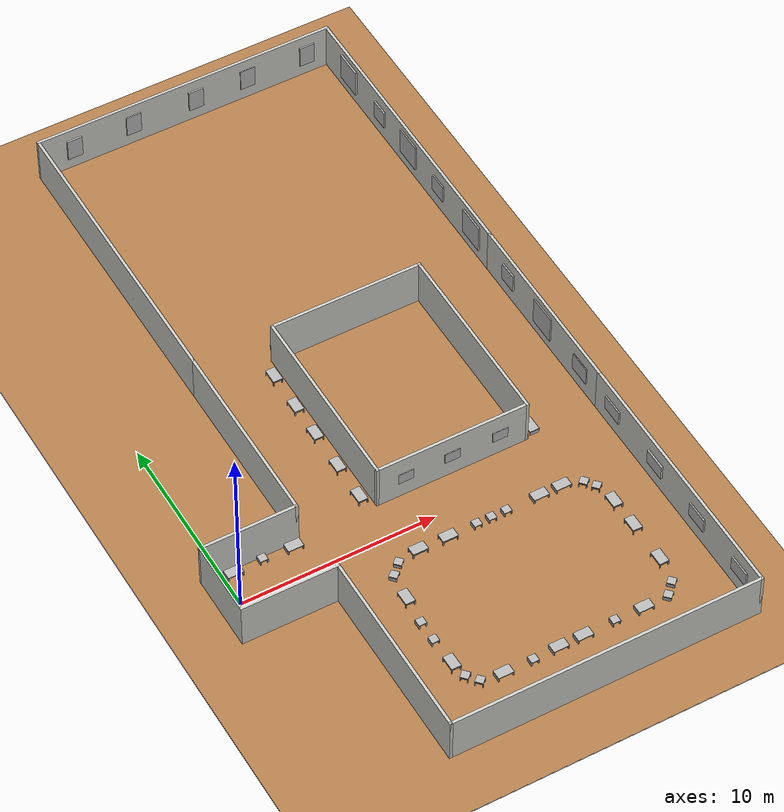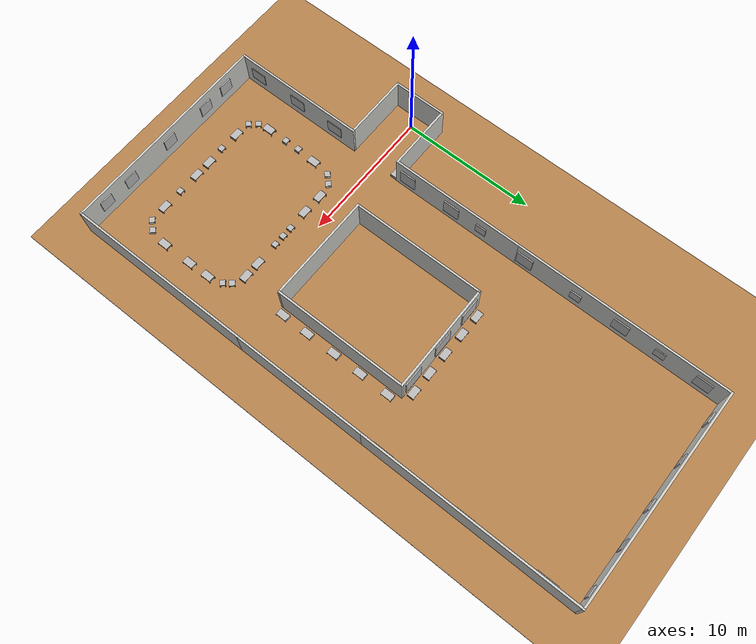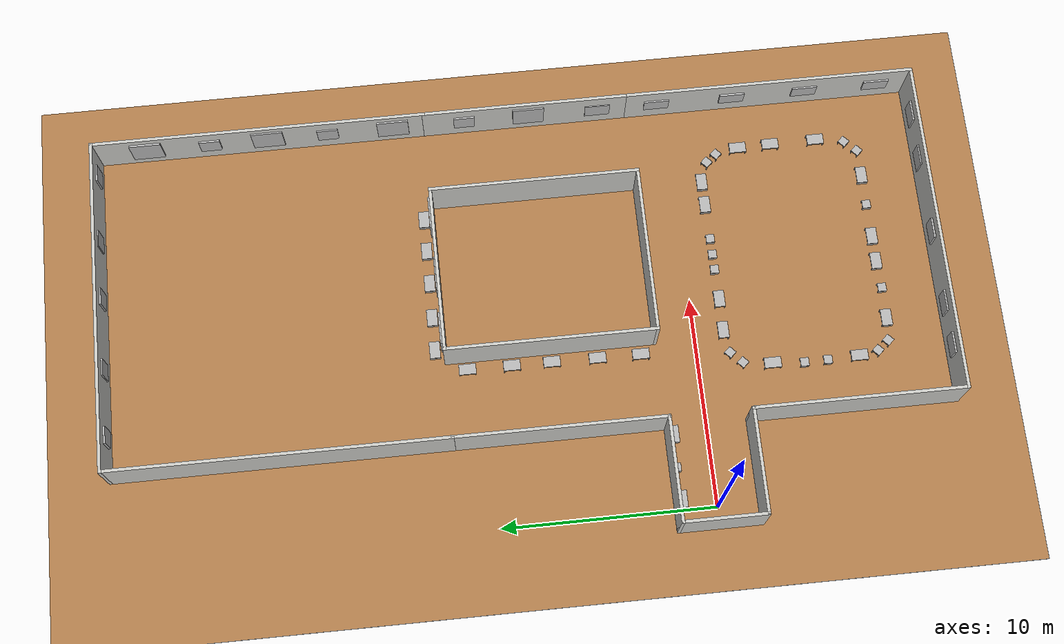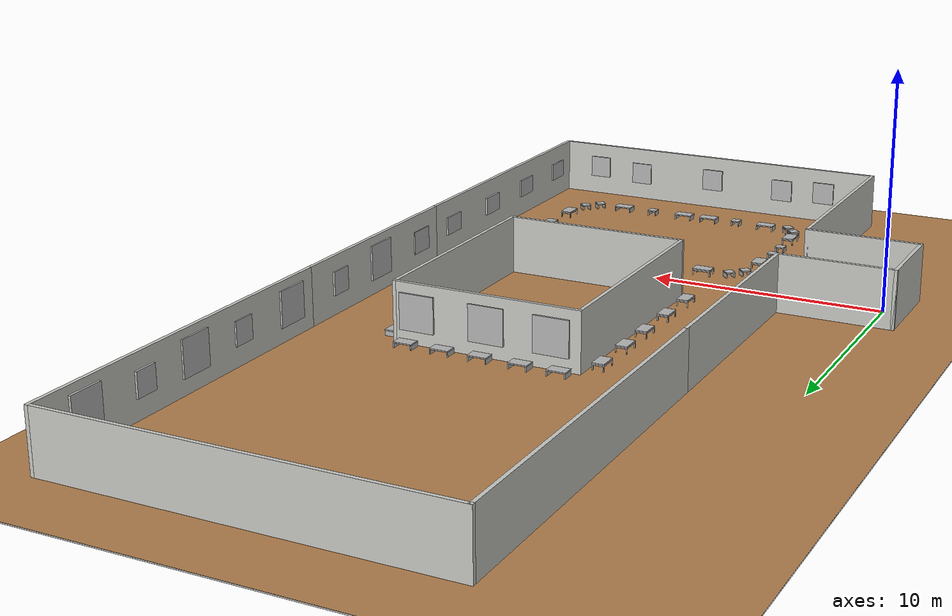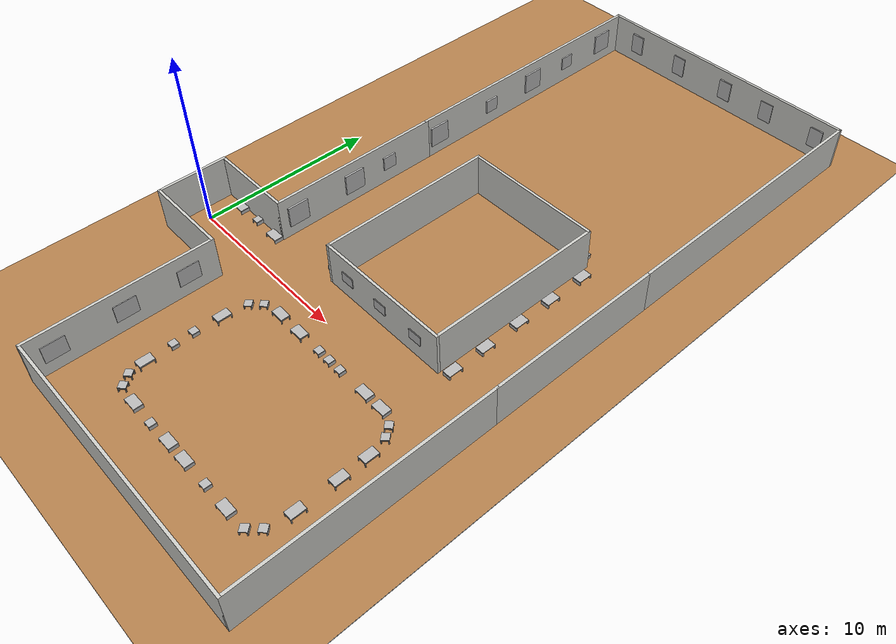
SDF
<sdf version="1.6">
 <world name="default">
  <light name="sun" type="directional">
   <pose>0 0 10 0 -0 0</pose>
   <diffuse>0.8 0.8 0.8 1</diffuse>
   <specular>0.2 0.2 0.2 1</specular>
   <attenuation>
    <range>1000</range>
    <constant>0.9</constant>
    <linear>0.01</linear>
    <quadratic>0.001</quadratic>
   </attenuation>
   <direction>-0.5 0.1 -0.9</direction>
  </light>
  <model name="ground_plane">
   <static>1</static>
   <link name="link">
    <collision name="collision">
     <geometry><plane><normal>0 0 1</normal><size>100 100</size></plane></geometry>
     <surface>
      <contact><collide_bitmask>65535</collide_bitmask></contact>
      <friction><ode><mu>100</mu><mu2>50</mu2></ode></friction>
     </surface>
    </collision>
    <visual name="visual">
     <cast_shadows>0</cast_shadows>
     <geometry><plane><normal>0 0 1</normal><size>100 100</size></plane></geometry>
     <material>
      <script><uri>file://media/materials/scripts/gazebo.material</uri><name>Gazebo/Grey</name></script>
     </material>
    </visual>
   </link>
  </model>
  <gravity>0 0 -9.8</gravity>
  <magnetic_field>6e-06 2.3e-05 -4.2e-05</magnetic_field>
  <atmosphere type="adiabatic"/>
  <physics name="default_physics" default="0" type="ode">
   <max_step_size>0.001</max_step_size>
   <real_time_factor>1</real_time_factor>
   <real_time_update_rate>1000</real_time_update_rate>
  </physics>
  <scene><ambient>0.4 0.4 0.4 1</ambient><background>0.7 0.7 0.7 1</background><shadows>1</shadows></scene>
  <audio><device>default</device></audio>
  <spherical_coordinates>
   <surface_model>EARTH_WGS84</surface_model>
   <latitude_deg>0</latitude_deg>
   <longitude_deg>0</longitude_deg>
   <elevation>0</elevation>
   <heading_deg>0</heading_deg>
  </spherical_coordinates>
  <model name="wood_floor_100">
   <pose>1.0299 1.49278 0 0 -0 0</pose>
   <link name="Wall_9">
    <collision name="Wall_9_Collision">
     <geometry><box><size>100.01 100 0.01</size></box></geometry>
     <pose>0 0 0.005 0 -0 0</pose>
    </collision>
    <visual name="Wall_9_Visual">
     <pose>0 0 0.005 0 -0 0</pose>
     <geometry><box><size>100.01 100 0.01</size></box></geometry>
     <material>
      <script><uri>file://media/materials/scripts/gazebo.material</uri><name>Gazebo/Wood</name></script>
      <ambient>1 1 1 1</ambient>
     </material>
     <meta><layer>0</layer></meta>
    </visual>
    <pose>-1e-06 -1e-06 0 0 -0 0</pose>
   </link>
   <static>1</static>
  </model>
  <model name="chair1">
   <link name="link">
    <inertial>
     <mass>3</mass>
     <inertia><ixx>1</ixx><ixy>0</ixy><ixz>0</ixz><iyy>1</iyy><iyz>0</iyz><izz>1</izz></inertia>
    </inertial>
    <collision name="left">
     <pose>0 0 0.2 0 -0 1.57</pose>
     <geometry><box><size>0.5 0.05 0.2</size></box></geometry>
    </collision>
    <visual name="visual1">
     <pose>0 0 0.2 0 -0 1.57</pose>
     <geometry><box><size>0.5 0.05 0.2</size></box></geometry>
     <material>
      <script>
       <uri>model://chair1/materials/test_texture_leg.material</uri>
       <name>TestTexturechairleg1</name>
      </script>
     </material>
    </visual>
    <collision name="right">
     <pose>0.75 0 0.2 0 -0 1.57</pose>
     <geometry><box><size>0.5 0.05 0.2</size></box></geometry>
    </collision>
    <visual name="visual2">
     <pose>0.75 0 0.2 0 -0 1.57</pose>
     <geometry><box><size>0.5 0.05 0.2</size></box></geometry>
     <material>
      <script>
       <uri>model://chair1/materials/test_texture_leg.material</uri>
       <name>TestTexturechairleg1</name>
      </script>
     </material>
    </visual>
    <collision name="top">
     <pose>0.375 0 0.325 0 -0 0</pose>
     <geometry><box><size>0.8 0.5 0.05</size></box></geometry>
    </collision>
    <visual name="visual3">
     <pose>0.375 0 0.325 0 -0 0</pose>
     <geometry><box><size>0.8 0.5 0.05</size></box></geometry>
     <material>
      <script>
       <uri>model://chair1/materials/test_texture_plane.material</uri>
       <name>TestTexturechairplane1</name>
      </script>
     </material>
    </visual>
   </link>
   <pose>0.13712 1.60346 -0.089999 2e-06 -0 -0.000142</pose>
  </model>
  <model name="chair2">
   <link name="link">
    <inertial>
     <mass>1.5</mass>
     <inertia><ixx>1</ixx><ixy>0</ixy><ixz>0</ixz><iyy>1</iyy><iyz>0</iyz><izz>1</izz></inertia>
    </inertial>
    <collision name="left">
     <pose>0 0 0.2 0 -0 1.57</pose>
     <geometry><box><size>0.4 0.05 0.2</size></box></geometry>
    </collision>
    <visual name="visual1">
     <pose>0 0 0.2 0 -0 1.57</pose>
     <geometry><box><size>0.4 0.05 0.2</size></box></geometry>
     <material>
      <script>
       <uri>model://chair2/materials/test_texture_leg.material</uri>
       <name>TestTexturechairleg2</name>
      </script>
     </material>
    </visual>
    <collision name="right">
     <pose>0.35 0 0.2 0 -0 1.57</pose>
     <geometry><box><size>0.4 0.05 0.2</size></box></geometry>
    </collision>
    <visual name="visual2">
     <pose>0.35 0 0.2 0 -0 1.57</pose>
     <geometry><box><size>0.4 0.05 0.2</size></box></geometry>
     <material>
      <script>
       <uri>model://chair2/materials/test_texture_leg.material</uri>
       <name>TestTexturechairleg2</name>
      </script>
     </material>
    </visual>
    <collision name="top">
     <pose>0.175 0 0.325 0 -0 0</pose>
     <geometry><box><size>0.4 0.4 0.05</size></box></geometry>
    </collision>
    <visual name="visual3">
     <pose>0.175 0 0.325 0 -0 0</pose>
     <geometry><box><size>0.4 0.4 0.05</size></box></geometry>
     <material>
      <script>
       <uri>model://chair2/materials/test_texture_plane.material</uri>
       <name>TestTexturechairplane2</name>
      </script>
     </material>
    </visual>
   </link>
   <pose>1.8308 1.65353 -0.09 0 0 -3.6e-05</pose>
  </model>
  <model name="chair1_0">
   <link name="link">
    <inertial>
     <mass>3</mass>
     <inertia><ixx>1</ixx><ixy>0</ixy><ixz>0</ixz><iyy>1</iyy><iyz>0</iyz><izz>1</izz></inertia>
    </inertial>
    <collision name="left">
     <pose>0 0 0.2 0 -0 1.57</pose>
     <geometry><box><size>0.5 0.05 0.2</size></box></geometry>
    </collision>
    <visual name="visual1">
     <pose>0 0 0.2 0 -0 1.57</pose>
     <geometry><box><size>0.5 0.05 0.2</size></box></geometry>
     <material>
      <script>
       <uri>model://chair1/materials/test_texture_leg.material</uri>
       <name>TestTexturechairleg1</name>
      </script>
     </material>
    </visual>
    <collision name="right">
     <pose>0.75 0 0.2 0 -0 1.57</pose>
     <geometry><box><size>0.5 0.05 0.2</size></box></geometry>
    </collision>
    <visual name="visual2">
     <pose>0.75 0 0.2 0 -0 1.57</pose>
     <geometry><box><size>0.5 0.05 0.2</size></box></geometry>
     <material>
      <script>
       <uri>model://chair1/materials/test_texture_leg.material</uri>
       <name>TestTexturechairleg1</name>
      </script>
     </material>
    </visual>
    <collision name="top">
     <pose>0.375 0 0.325 0 -0 0</pose>
     <geometry><box><size>0.8 0.5 0.05</size></box></geometry>
    </collision>
    <visual name="visual3">
     <pose>0.375 0 0.325 0 -0 0</pose>
     <geometry><box><size>0.8 0.5 0.05</size></box></geometry>
     <material>
      <script>
       <uri>model://chair1/materials/test_texture_plane.material</uri>
       <name>TestTexturechairplane1</name>
      </script>
     </material>
    </visual>
   </link>
   <pose>3.20048 1.6029 -0.090007 -2e-06 -1e-06 -0.000678</pose>
  </model>
  <model name="chair2_0">
   <link name="link">
    <inertial>
     <mass>1.5</mass>
     <inertia><ixx>1</ixx><ixy>0</ixy><ixz>0</ixz><iyy>1</iyy><iyz>0</iyz><izz>1</izz></inertia>
    </inertial>
    <collision name="left">
     <pose>0 0 0.2 0 -0 1.57</pose>
     <geometry><box><size>0.4 0.05 0.2</size></box></geometry>
    </collision>
    <visual name="visual1">
     <pose>0 0 0.2 0 -0 1.57</pose>
     <geometry><box><size>0.4 0.05 0.2</size></box></geometry>
     <material>
      <script>
       <uri>model://chair2/materials/test_texture_leg.material</uri>
       <name>TestTexturechairleg2</name>
      </script>
     </material>
    </visual>
    <collision name="right">
     <pose>0.35 0 0.2 0 -0 1.57</pose>
     <geometry><box><size>0.4 0.05 0.2</size></box></geometry>
    </collision>
    <visual name="visual2">
     <pose>0.35 0 0.2 0 -0 1.57</pose>
     <geometry><box><size>0.4 0.05 0.2</size></box></geometry>
     <material>
      <script>
       <uri>model://chair2/materials/test_texture_leg.material</uri>
       <name>TestTexturechairleg2</name>
      </script>
     </material>
    </visual>
    <collision name="top">
     <pose>0.175 0 0.325 0 -0 0</pose>
     <geometry><box><size>0.4 0.4 0.05</size></box></geometry>
    </collision>
    <visual name="visual3">
     <pose>0.175 0 0.325 0 -0 0</pose>
     <geometry><box><size>0.4 0.4 0.05</size></box></geometry>
     <material>
      <script>
       <uri>model://chair2/materials/test_texture_plane.material</uri>
       <name>TestTexturechairplane2</name>
      </script>
     </material>
    </visual>
   </link>
   <pose>11.1966 -1.36081 -0.09001 0 -0 -6e-06</pose>
  </model>
  <model name="chair2_1">
   <link name="link">
    <inertial>
     <mass>1.5</mass>
     <inertia><ixx>1</ixx><ixy>0</ixy><ixz>0</ixz><iyy>1</iyy><iyz>0</iyz><izz>1</izz></inertia>
    </inertial>
    <collision name="left">
     <pose>0 0 0.2 0 -0 1.57</pose>
     <geometry><box><size>0.4 0.05 0.2</size></box></geometry>
    </collision>
    <visual name="visual1">
     <pose>0 0 0.2 0 -0 1.57</pose>
     <geometry><box><size>0.4 0.05 0.2</size></box></geometry>
     <material>
      <script>
       <uri>model://chair2/materials/test_texture_leg.material</uri>
       <name>TestTexturechairleg2</name>
      </script>
     </material>
    </visual>
    <collision name="right">
     <pose>0.35 0 0.2 0 -0 1.57</pose>
     <geometry><box><size>0.4 0.05 0.2</size></box></geometry>
    </collision>
    <visual name="visual2">
     <pose>0.35 0 0.2 0 -0 1.57</pose>
     <geometry><box><size>0.4 0.05 0.2</size></box></geometry>
     <material>
      <script>
       <uri>model://chair2/materials/test_texture_leg.material</uri>
       <name>TestTexturechairleg2</name>
      </script>
     </material>
    </visual>
    <collision name="top">
     <pose>0.175 0 0.325 0 -0 0</pose>
     <geometry><box><size>0.4 0.4 0.05</size></box></geometry>
    </collision>
    <visual name="visual3">
     <pose>0.175 0 0.325 0 -0 0</pose>
     <geometry><box><size>0.4 0.4 0.05</size></box></geometry>
     <material>
      <script>
       <uri>model://chair2/materials/test_texture_plane.material</uri>
       <name>TestTexturechairplane2</name>
      </script>
     </material>
    </visual>
   </link>
   <pose>11.9632 -1.36081 -0.09 0 0 -5e-06</pose>
  </model>
  <model name="chair2_2">
   <link name="link">
    <inertial>
     <mass>1.5</mass>
     <inertia><ixx>1</ixx><ixy>0</ixy><ixz>0</ixz><iyy>1</iyy><iyz>0</iyz><izz>1</izz></inertia>
    </inertial>
    <collision name="left">
     <pose>0 0 0.2 0 -0 1.57</pose>
     <geometry><box><size>0.4 0.05 0.2</size></box></geometry>
    </collision>
    <visual name="visual1">
     <pose>0 0 0.2 0 -0 1.57</pose>
     <geometry><box><size>0.4 0.05 0.2</size></box></geometry>
     <material>
      <script>
       <uri>model://chair2/materials/test_texture_leg.material</uri>
       <name>TestTexturechairleg2</name>
      </script>
     </material>
    </visual>
    <collision name="right">
     <pose>0.35 0 0.2 0 -0 1.57</pose>
     <geometry><box><size>0.4 0.05 0.2</size></box></geometry>
    </collision>
    <visual name="visual2">
     <pose>0.35 0 0.2 0 -0 1.57</pose>
     <geometry><box><size>0.4 0.05 0.2</size></box></geometry>
     <material>
      <script>
       <uri>model://chair2/materials/test_texture_leg.material</uri>
       <name>TestTexturechairleg2</name>
      </script>
     </material>
    </visual>
    <collision name="top">
     <pose>0.175 0 0.325 0 -0 0</pose>
     <geometry><box><size>0.4 0.4 0.05</size></box></geometry>
    </collision>
    <visual name="visual3">
     <pose>0.175 0 0.325 0 -0 0</pose>
     <geometry><box><size>0.4 0.4 0.05</size></box></geometry>
     <material>
      <script>
       <uri>model://chair2/materials/test_texture_plane.material</uri>
       <name>TestTexturechairplane2</name>
      </script>
     </material>
    </visual>
   </link>
   <pose>12.7574 -1.36081 -0.09 0 -0 0</pose>
  </model>
  <model name="chair1_3">
   <link name="link">
    <inertial>
     <mass>3</mass>
     <inertia><ixx>1</ixx><ixy>0</ixy><ixz>0</ixz><iyy>1</iyy><iyz>0</iyz><izz>1</izz></inertia>
    </inertial>
    <collision name="left">
     <pose>0 0 0.2 0 -0 1.57</pose>
     <geometry><box><size>0.5 0.05 0.2</size></box></geometry>
    </collision>
    <visual name="visual1">
     <pose>0 0 0.2 0 -0 1.57</pose>
     <geometry><box><size>0.5 0.05 0.2</size></box></geometry>
     <material>
      <script>
       <uri>model://chair1/materials/test_texture_leg.material</uri>
       <name>TestTexturechairleg1</name>
      </script>
     </material>
    </visual>
    <collision name="right">
     <pose>0.75 0 0.2 0 -0 1.57</pose>
     <geometry><box><size>0.5 0.05 0.2</size></box></geometry>
    </collision>
    <visual name="visual2">
     <pose>0.75 0 0.2 0 -0 1.57</pose>
     <geometry><box><size>0.5 0.05 0.2</size></box></geometry>
     <material>
      <script>
       <uri>model://chair1/materials/test_texture_leg.material</uri>
       <name>TestTexturechairleg1</name>
      </script>
     </material>
    </visual>
    <collision name="top">
     <pose>0.375 0 0.325 0 -0 0</pose>
     <geometry><box><size>0.8 0.5 0.05</size></box></geometry>
    </collision>
    <visual name="visual3">
     <pose>0.375 0 0.325 0 -0 0</pose>
     <geometry><box><size>0.8 0.5 0.05</size></box></geometry>
     <material>
      <script>
       <uri>model://chair1/materials/test_texture_plane.material</uri>
       <name>TestTexturechairplane1</name>
      </script>
     </material>
    </visual>
   </link>
   <pose>14.3179 -1.33335 -0.090007 -2e-06 -1e-06 0.00158</pose>
  </model>
  <model name="chair1_4">
   <link name="link">
    <inertial>
     <mass>3</mass>
     <inertia><ixx>1</ixx><ixy>0</ixy><ixz>0</ixz><iyy>1</iyy><iyz>0</iyz><izz>1</izz></inertia>
    </inertial>
    <collision name="left">
     <pose>0 0 0.2 0 -0 1.57</pose>
     <geometry><box><size>0.5 0.05 0.2</size></box></geometry>
    </collision>
    <visual name="visual1">
     <pose>0 0 0.2 0 -0 1.57</pose>
     <geometry><box><size>0.5 0.05 0.2</size></box></geometry>
     <material>
      <script>
       <uri>model://chair1/materials/test_texture_leg.material</uri>
       <name>TestTexturechairleg1</name>
      </script>
     </material>
    </visual>
    <collision name="right">
     <pose>0.75 0 0.2 0 -0 1.57</pose>
     <geometry><box><size>0.5 0.05 0.2</size></box></geometry>
    </collision>
    <visual name="visual2">
     <pose>0.75 0 0.2 0 -0 1.57</pose>
     <geometry><box><size>0.5 0.05 0.2</size></box></geometry>
     <material>
      <script>
       <uri>model://chair1/materials/test_texture_leg.material</uri>
       <name>TestTexturechairleg1</name>
      </script>
     </material>
    </visual>
    <collision name="top">
     <pose>0.375 0 0.325 0 -0 0</pose>
     <geometry><box><size>0.8 0.5 0.05</size></box></geometry>
    </collision>
    <visual name="visual3">
     <pose>0.375 0 0.325 0 -0 0</pose>
     <geometry><box><size>0.8 0.5 0.05</size></box></geometry>
     <material>
      <script>
       <uri>model://chair1/materials/test_texture_plane.material</uri>
       <name>TestTexturechairplane1</name>
      </script>
     </material>
    </visual>
   </link>
   <pose>15.4952 -1.33335 -0.089999 2e-06 -0 0.001563</pose>
  </model>
  <model name="chair4">
   <link name="link">
    <inertial>
     <mass>1.5</mass>
     <inertia><ixx>1</ixx><ixy>0</ixy><ixz>0</ixz><iyy>1</iyy><iyz>0</iyz><izz>1</izz></inertia>
    </inertial>
    <collision name="left1">
     <pose>0 0.175 0.2 0 -0 1.57</pose>
     <geometry><box><size>0.05 0.05 0.2</size></box></geometry>
    </collision>
    <visual name="visual1">
     <pose>0 0.175 0.2 0 -0 1.57</pose>
     <geometry><box><size>0.05 0.05 0.2</size></box></geometry>
     <material>
      <script>
       <uri>model://chair4/materials/test_texture_leg.material</uri>
       <name>TestTexturechairleg4</name>
      </script>
     </material>
    </visual>
    <collision name="right1">
     <pose>0.35 0.175 0.2 0 -0 1.57</pose>
     <geometry><box><size>0.05 0.05 0.2</size></box></geometry>
    </collision>
    <visual name="visual2">
     <pose>0.35 0.175 0.2 0 -0 1.57</pose>
     <geometry><box><size>0.05 0.05 0.2</size></box></geometry>
     <material>
      <script>
       <uri>model://chair4/materials/test_texture_leg.material</uri>
       <name>TestTexturechairleg4</name>
      </script>
     </material>
    </visual>
    <collision name="left2">
     <pose>0 -0.175 0.2 0 -0 1.57</pose>
     <geometry><box><size>0.05 0.05 0.2</size></box></geometry>
    </collision>
    <visual name="visual3">
     <pose>0 -0.175 0.2 0 -0 1.57</pose>
     <geometry><box><size>0.05 0.05 0.2</size></box></geometry>
     <material>
      <script>
       <uri>model://chair4/materials/test_texture_leg.material</uri>
       <name>TestTexturechairleg4</name>
      </script>
     </material>
    </visual>
    <collision name="right2">
     <pose>0.35 -0.175 0.2 0 -0 1.57</pose>
     <geometry><box><size>0.05 0.05 0.2</size></box></geometry>
    </collision>
    <visual name="visual4">
     <pose>0.35 -0.175 0.2 0 -0 1.57</pose>
     <geometry><box><size>0.05 0.05 0.2</size></box></geometry>
     <material>
      <script>
       <uri>model://chair4/materials/test_texture_leg.material</uri>
       <name>TestTexturechairleg4</name>
      </script>
     </material>
    </visual>
    <collision name="top">
     <pose>0.175 0 0.375 0 -0 0</pose>
     <geometry><box><size>0.4 0.4 0.05</size></box></geometry>
    </collision>
    <visual name="visual11">
     <pose>0.175 0 0.375 0 -0 0</pose>
     <geometry><box><size>0.4 0.4 0.05</size></box></geometry>
     <material>
      <script>
       <uri>model://chair4/materials/test_texture_plane.material</uri>
       <name>TestTexturechairplane4</name>
      </script>
     </material>
    </visual>
    <collision name="top2">
     <pose>0.175 0 0.325 0 -0 0</pose>
     <geometry><box><size>0.4 0.4 0.05</size></box></geometry>
    </collision>
    <visual name="visual12">
     <pose>0.175 0 0.325 0 -0 0</pose>
     <geometry><box><size>0.4 0.4 0.05</size></box></geometry>
     <material>
      <script>
       <uri>model://chair4/materials/test_texture_leg.material</uri>
       <name>TestTexturechairleg4</name>
      </script>
     </material>
    </visual>
   </link>
   <pose>16.7096 -1.8199 -0.09 -0 -1e-06 0.749723</pose>
  </model>
  <model name="chair4_clone">
   <link name="link">
    <inertial>
     <mass>1.5</mass>
     <inertia><ixx>1</ixx><ixy>0</ixy><ixz>0</ixz><iyy>1</iyy><iyz>0</iyz><izz>1</izz></inertia>
    </inertial>
    <collision name="left1">
     <pose>0 0.175 0.2 0 -0 1.57</pose>
     <geometry><box><size>0.05 0.05 0.2</size></box></geometry>
    </collision>
    <visual name="visual1">
     <pose>0 0.175 0.2 0 -0 1.57</pose>
     <geometry><box><size>0.05 0.05 0.2</size></box></geometry>
     <material>
      <script>
       <uri>model://chair4/materials/test_texture_leg.material</uri>
       <name>TestTexturechairleg4</name>
      </script>
     </material>
    </visual>
    <collision name="right1">
     <pose>0.35 0.175 0.2 0 -0 1.57</pose>
     <geometry><box><size>0.05 0.05 0.2</size></box></geometry>
    </collision>
    <visual name="visual2">
     <pose>0.35 0.175 0.2 0 -0 1.57</pose>
     <geometry><box><size>0.05 0.05 0.2</size></box></geometry>
     <material>
      <script>
       <uri>model://chair4/materials/test_texture_leg.material</uri>
       <name>TestTexturechairleg4</name>
      </script>
     </material>
    </visual>
    <collision name="left2">
     <pose>0 -0.175 0.2 0 -0 1.57</pose>
     <geometry><box><size>0.05 0.05 0.2</size></box></geometry>
    </collision>
    <visual name="visual3">
     <pose>0 -0.175 0.2 0 -0 1.57</pose>
     <geometry><box><size>0.05 0.05 0.2</size></box></geometry>
     <material>
      <script>
       <uri>model://chair4/materials/test_texture_leg.material</uri>
       <name>TestTexturechairleg4</name>
      </script>
     </material>
    </visual>
    <collision name="right2">
     <pose>0.35 -0.175 0.2 0 -0 1.57</pose>
     <geometry><box><size>0.05 0.05 0.2</size></box></geometry>
    </collision>
    <visual name="visual4">
     <pose>0.35 -0.175 0.2 0 -0 1.57</pose>
     <geometry><box><size>0.05 0.05 0.2</size></box></geometry>
     <material>
      <script>
       <uri>model://chair4/materials/test_texture_leg.material</uri>
       <name>TestTexturechairleg4</name>
      </script>
     </material>
    </visual>
    <collision name="top">
     <pose>0.175 0 0.375 0 -0 0</pose>
     <geometry><box><size>0.4 0.4 0.05</size></box></geometry>
    </collision>
    <visual name="visual11">
     <pose>0.175 0 0.375 0 -0 0</pose>
     <geometry><box><size>0.4 0.4 0.05</size></box></geometry>
     <material>
      <script>
       <uri>model://chair4/materials/test_texture_plane.material</uri>
       <name>TestTexturechairplane4</name>
      </script>
     </material>
    </visual>
    <collision name="top2">
     <pose>0.175 0 0.325 0 -0 0</pose>
     <geometry><box><size>0.4 0.4 0.05</size></box></geometry>
    </collision>
    <visual name="visual12">
     <pose>0.175 0 0.325 0 -0 0</pose>
     <geometry><box><size>0.4 0.4 0.05</size></box></geometry>
     <material>
      <script>
       <uri>model://chair4/materials/test_texture_leg.material</uri>
       <name>TestTexturechairleg4</name>
      </script>
     </material>
    </visual>
   </link>
   <pose>17.0857 -2.31775 -0.090006 -1e-06 -1e-06 0.749733</pose>
  </model>
  <model name="chair3">
   <link name="link">
    <inertial>
     <mass>3</mass>
     <inertia><ixx>1</ixx><ixy>0</ixy><ixz>0</ixz><iyy>1</iyy><iyz>0</iyz><izz>1</izz></inertia>
    </inertial>
    <collision name="left1">
     <pose>0 0.225 0.2 0 -0 1.57</pose>
     <geometry><box><size>0.05 0.05 0.2</size></box></geometry>
    </collision>
    <visual name="visual1">
     <pose>0 0.225 0.2 0 -0 1.57</pose>
     <geometry><box><size>0.05 0.05 0.2</size></box></geometry>
     <material>
      <script>
       <uri>model://chair3/materials/test_texture_leg.material</uri>
       <name>TestTexturechairleg3</name>
      </script>
     </material>
    </visual>
    <collision name="right1">
     <pose>0.75 0.225 0.2 0 -0 1.57</pose>
     <geometry><box><size>0.05 0.05 0.2</size></box></geometry>
    </collision>
    <visual name="visual2">
     <pose>0.75 0.225 0.2 0 -0 1.57</pose>
     <geometry><box><size>0.05 0.05 0.2</size></box></geometry>
     <material>
      <script>
       <uri>model://chair3/materials/test_texture_leg.material</uri>
       <name>TestTexturechairleg3</name>
      </script>
     </material>
    </visual>
    <collision name="left2">
     <pose>0 -0.225 0.2 0 -0 1.57</pose>
     <geometry><box><size>0.05 0.05 0.2</size></box></geometry>
    </collision>
    <visual name="visual3">
     <pose>0 -0.225 0.2 0 -0 1.57</pose>
     <geometry><box><size>0.05 0.05 0.2</size></box></geometry>
     <material>
      <script>
       <uri>model://chair3/materials/test_texture_leg.material</uri>
       <name>TestTexturechairleg3</name>
      </script>
     </material>
    </visual>
    <collision name="right2">
     <pose>0.75 -0.225 0.2 0 -0 1.57</pose>
     <geometry><box><size>0.05 0.05 0.2</size></box></geometry>
    </collision>
    <visual name="visual4">
     <pose>0.75 -0.225 0.2 0 -0 1.57</pose>
     <geometry><box><size>0.05 0.05 0.2</size></box></geometry>
     <material>
      <script>
       <uri>model://chair3/materials/test_texture_leg.material</uri>
       <name>TestTexturechairleg3</name>
      </script>
     </material>
    </visual>
    <collision name="top">
     <pose>0.375 0 0.375 0 -0 0</pose>
     <geometry><box><size>0.8 0.5 0.05</size></box></geometry>
    </collision>
    <visual name="visual11">
     <pose>0.375 0 0.375 0 -0 0</pose>
     <geometry><box><size>0.8 0.5 0.05</size></box></geometry>
     <material>
      <script>
       <uri>model://chair3/materials/test_texture_plane.material</uri>
       <name>TestTexturechairplane3</name>
      </script>
     </material>
    </visual>
    <collision name="top2">
     <pose>0.375 0 0.325 0 -0 0</pose>
     <geometry><box><size>0.8 0.5 0.05</size></box></geometry>
    </collision>
    <visual name="visual12">
     <pose>0.375 0 0.325 0 -0 0</pose>
     <geometry><box><size>0.8 0.5 0.05</size></box></geometry>
     <material>
      <script>
       <uri>model://chair3/materials/test_texture_leg.material</uri>
       <name>TestTexturechairleg3</name>
      </script>
     </material>
    </visual>
   </link>
   <pose>17.4534 -3.67478 -0.090008 2e-06 -0 1.56996</pose>
  </model>
  <model name="chair3_clone">
   <link name="link">
    <inertial>
     <mass>3</mass>
     <inertia><ixx>1</ixx><ixy>0</ixy><ixz>0</ixz><iyy>1</iyy><iyz>0</iyz><izz>1</izz></inertia>
    </inertial>
    <collision name="left1">
     <pose>0 0.225 0.2 0 -0 1.57</pose>
     <geometry><box><size>0.05 0.05 0.2</size></box></geometry>
    </collision>
    <visual name="visual1">
     <pose>0 0.225 0.2 0 -0 1.57</pose>
     <geometry><box><size>0.05 0.05 0.2</size></box></geometry>
     <material>
      <script>
       <uri>model://chair3/materials/test_texture_leg.material</uri>
       <name>TestTexturechairleg3</name>
      </script>
     </material>
    </visual>
    <collision name="right1">
     <pose>0.75 0.225 0.2 0 -0 1.57</pose>
     <geometry><box><size>0.05 0.05 0.2</size></box></geometry>
    </collision>
    <visual name="visual2">
     <pose>0.75 0.225 0.2 0 -0 1.57</pose>
     <geometry><box><size>0.05 0.05 0.2</size></box></geometry>
     <material>
      <script>
       <uri>model://chair3/materials/test_texture_leg.material</uri>
       <name>TestTexturechairleg3</name>
      </script>
     </material>
    </visual>
    <collision name="left2">
     <pose>0 -0.225 0.2 0 -0 1.57</pose>
     <geometry><box><size>0.05 0.05 0.2</size></box></geometry>
    </collision>
    <visual name="visual3">
     <pose>0 -0.225 0.2 0 -0 1.57</pose>
     <geometry><box><size>0.05 0.05 0.2</size></box></geometry>
     <material>
      <script>
       <uri>model://chair3/materials/test_texture_leg.material</uri>
       <name>TestTexturechairleg3</name>
      </script>
     </material>
    </visual>
    <collision name="right2">
     <pose>0.75 -0.225 0.2 0 -0 1.57</pose>
     <geometry><box><size>0.05 0.05 0.2</size></box></geometry>
    </collision>
    <visual name="visual4">
     <pose>0.75 -0.225 0.2 0 -0 1.57</pose>
     <geometry><box><size>0.05 0.05 0.2</size></box></geometry>
     <material>
      <script>
       <uri>model://chair3/materials/test_texture_leg.material</uri>
       <name>TestTexturechairleg3</name>
      </script>
     </material>
    </visual>
    <collision name="top">
     <pose>0.375 0 0.375 0 -0 0</pose>
     <geometry><box><size>0.8 0.5 0.05</size></box></geometry>
    </collision>
    <visual name="visual11">
     <pose>0.375 0 0.375 0 -0 0</pose>
     <geometry><box><size>0.8 0.5 0.05</size></box></geometry>
     <material>
      <script>
       <uri>model://chair3/materials/test_texture_plane.material</uri>
       <name>TestTexturechairplane3</name>
      </script>
     </material>
    </visual>
    <collision name="top2">
     <pose>0.375 0 0.325 0 -0 0</pose>
     <geometry><box><size>0.8 0.5 0.05</size></box></geometry>
    </collision>
    <visual name="visual12">
     <pose>0.375 0 0.325 0 -0 0</pose>
     <geometry><box><size>0.8 0.5 0.05</size></box></geometry>
     <material>
      <script>
       <uri>model://chair3/materials/test_texture_leg.material</uri>
       <name>TestTexturechairleg3</name>
      </script>
     </material>
    </visual>
   </link>
   <pose>17.4959 -5.27853 -0.090002 -2e-06 -0 1.56997</pose>
  </model>
  <model name="chair3_clone_clone">
   <link name="link">
    <inertial>
     <mass>3</mass>
     <inertia><ixx>1</ixx><ixy>0</ixy><ixz>0</ixz><iyy>1</iyy><iyz>0</iyz><izz>1</izz></inertia>
    </inertial>
    <collision name="left1">
     <pose>0 0.225 0.2 0 -0 1.57</pose>
     <geometry><box><size>0.05 0.05 0.2</size></box></geometry>
    </collision>
    <visual name="visual1">
     <pose>0 0.225 0.2 0 -0 1.57</pose>
     <geometry><box><size>0.05 0.05 0.2</size></box></geometry>
     <material>
      <script>
       <uri>model://chair3/materials/test_texture_leg.material</uri>
       <name>TestTexturechairleg3</name>
      </script>
     </material>
    </visual>
    <collision name="right1">
     <pose>0.75 0.225 0.2 0 -0 1.57</pose>
     <geometry><box><size>0.05 0.05 0.2</size></box></geometry>
    </collision>
    <visual name="visual2">
     <pose>0.75 0.225 0.2 0 -0 1.57</pose>
     <geometry><box><size>0.05 0.05 0.2</size></box></geometry>
     <material>
      <script>
       <uri>model://chair3/materials/test_texture_leg.material</uri>
       <name>TestTexturechairleg3</name>
      </script>
     </material>
    </visual>
    <collision name="left2">
     <pose>0 -0.225 0.2 0 -0 1.57</pose>
     <geometry><box><size>0.05 0.05 0.2</size></box></geometry>
    </collision>
    <visual name="visual3">
     <pose>0 -0.225 0.2 0 -0 1.57</pose>
     <geometry><box><size>0.05 0.05 0.2</size></box></geometry>
     <material>
      <script>
       <uri>model://chair3/materials/test_texture_leg.material</uri>
       <name>TestTexturechairleg3</name>
      </script>
     </material>
    </visual>
    <collision name="right2">
     <pose>0.75 -0.225 0.2 0 -0 1.57</pose>
     <geometry><box><size>0.05 0.05 0.2</size></box></geometry>
    </collision>
    <visual name="visual4">
     <pose>0.75 -0.225 0.2 0 -0 1.57</pose>
     <geometry><box><size>0.05 0.05 0.2</size></box></geometry>
     <material>
      <script>
       <uri>model://chair3/materials/test_texture_leg.material</uri>
       <name>TestTexturechairleg3</name>
      </script>
     </material>
    </visual>
    <collision name="top">
     <pose>0.375 0 0.375 0 -0 0</pose>
     <geometry><box><size>0.8 0.5 0.05</size></box></geometry>
    </collision>
    <visual name="visual11">
     <pose>0.375 0 0.375 0 -0 0</pose>
     <geometry><box><size>0.8 0.5 0.05</size></box></geometry>
     <material>
      <script>
       <uri>model://chair3/materials/test_texture_plane.material</uri>
       <name>TestTexturechairplane3</name>
      </script>
     </material>
    </visual>
    <collision name="top2">
     <pose>0.375 0 0.325 0 -0 0</pose>
     <geometry><box><size>0.8 0.5 0.05</size></box></geometry>
    </collision>
    <visual name="visual12">
     <pose>0.375 0 0.325 0 -0 0</pose>
     <geometry><box><size>0.8 0.5 0.05</size></box></geometry>
     <material>
      <script>
       <uri>model://chair3/materials/test_texture_leg.material</uri>
       <name>TestTexturechairleg3</name>
      </script>
     </material>
    </visual>
   </link>
   <pose>17.5105 -7.50326 -0.090009 1e-06 -0 1.56995</pose>
  </model>
  <model name="chair2_3">
   <link name="link">
    <inertial>
     <mass>1.5</mass>
     <inertia><ixx>1</ixx><ixy>0</ixy><ixz>0</ixz><iyy>1</iyy><iyz>0</iyz><izz>1</izz></inertia>
    </inertial>
    <collision name="left">
     <pose>0 0 0.2 0 -0 1.57</pose>
     <geometry><box><size>0.4 0.05 0.2</size></box></geometry>
    </collision>
    <visual name="visual1">
     <pose>0 0 0.2 0 -0 1.57</pose>
     <geometry><box><size>0.4 0.05 0.2</size></box></geometry>
     <material>
      <script>
       <uri>model://chair2/materials/test_texture_leg.material</uri>
       <name>TestTexturechairleg2</name>
      </script>
     </material>
    </visual>
    <collision name="right">
     <pose>0.35 0 0.2 0 -0 1.57</pose>
     <geometry><box><size>0.4 0.05 0.2</size></box></geometry>
    </collision>
    <visual name="visual2">
     <pose>0.35 0 0.2 0 -0 1.57</pose>
     <geometry><box><size>0.4 0.05 0.2</size></box></geometry>
     <material>
      <script>
       <uri>model://chair2/materials/test_texture_leg.material</uri>
       <name>TestTexturechairleg2</name>
      </script>
     </material>
    </visual>
    <collision name="top">
     <pose>0.175 0 0.325 0 -0 0</pose>
     <geometry><box><size>0.4 0.4 0.05</size></box></geometry>
    </collision>
    <visual name="visual3">
     <pose>0.175 0 0.325 0 -0 0</pose>
     <geometry><box><size>0.4 0.4 0.05</size></box></geometry>
     <material>
      <script>
       <uri>model://chair2/materials/test_texture_plane.material</uri>
       <name>TestTexturechairplane2</name>
      </script>
     </material>
    </visual>
   </link>
   <pose>17.1463 -8.63413 -0.090009 0 -0 0.750016</pose>
  </model>
  <model name="chair2_3_clone">
   <link name="link">
    <inertial>
     <mass>1.5</mass>
     <inertia><ixx>1</ixx><ixy>0</ixy><ixz>0</ixz><iyy>1</iyy><iyz>0</iyz><izz>1</izz></inertia>
    </inertial>
    <collision name="left">
     <pose>0 0 0.2 0 -0 1.57</pose>
     <geometry><box><size>0.4 0.05 0.2</size></box></geometry>
    </collision>
    <visual name="visual1">
     <pose>0 0 0.2 0 -0 1.57</pose>
     <geometry><box><size>0.4 0.05 0.2</size></box></geometry>
     <material>
      <script>
       <uri>model://chair2/materials/test_texture_leg.material</uri>
       <name>TestTexturechairleg2</name>
      </script>
     </material>
    </visual>
    <collision name="right">
     <pose>0.35 0 0.2 0 -0 1.57</pose>
     <geometry><box><size>0.4 0.05 0.2</size></box></geometry>
    </collision>
    <visual name="visual2">
     <pose>0.35 0 0.2 0 -0 1.57</pose>
     <geometry><box><size>0.4 0.05 0.2</size></box></geometry>
     <material>
      <script>
       <uri>model://chair2/materials/test_texture_leg.material</uri>
       <name>TestTexturechairleg2</name>
      </script>
     </material>
    </visual>
    <collision name="top">
     <pose>0.175 0 0.325 0 -0 0</pose>
     <geometry><box><size>0.4 0.4 0.05</size></box></geometry>
    </collision>
    <visual name="visual3">
     <pose>0.175 0 0.325 0 -0 0</pose>
     <geometry><box><size>0.4 0.4 0.05</size></box></geometry>
     <material>
      <script>
       <uri>model://chair2/materials/test_texture_plane.material</uri>
       <name>TestTexturechairplane2</name>
      </script>
     </material>
    </visual>
   </link>
   <pose>16.613 -9.19811 -0.090001 0 -0 0.749984</pose>
  </model>
  <model name="chair1_5">
   <link name="link">
    <inertial>
     <mass>3</mass>
     <inertia><ixx>1</ixx><ixy>0</ixy><ixz>0</ixz><iyy>1</iyy><iyz>0</iyz><izz>1</izz></inertia>
    </inertial>
    <collision name="left">
     <pose>0 0 0.2 0 -0 1.57</pose>
     <geometry><box><size>0.5 0.05 0.2</size></box></geometry>
    </collision>
    <visual name="visual1">
     <pose>0 0 0.2 0 -0 1.57</pose>
     <geometry><box><size>0.5 0.05 0.2</size></box></geometry>
     <material>
      <script>
       <uri>model://chair1/materials/test_texture_leg.material</uri>
       <name>TestTexturechairleg1</name>
      </script>
     </material>
    </visual>
    <collision name="right">
     <pose>0.75 0 0.2 0 -0 1.57</pose>
     <geometry><box><size>0.5 0.05 0.2</size></box></geometry>
    </collision>
    <visual name="visual2">
     <pose>0.75 0 0.2 0 -0 1.57</pose>
     <geometry><box><size>0.5 0.05 0.2</size></box></geometry>
     <material>
      <script>
       <uri>model://chair1/materials/test_texture_leg.material</uri>
       <name>TestTexturechairleg1</name>
      </script>
     </material>
    </visual>
    <collision name="top">
     <pose>0.375 0 0.325 0 -0 0</pose>
     <geometry><box><size>0.8 0.5 0.05</size></box></geometry>
    </collision>
    <visual name="visual3">
     <pose>0.375 0 0.325 0 -0 0</pose>
     <geometry><box><size>0.8 0.5 0.05</size></box></geometry>
     <material>
      <script>
       <uri>model://chair1/materials/test_texture_plane.material</uri>
       <name>TestTexturechairplane1</name>
      </script>
     </material>
    </visual>
   </link>
   <pose>15.0855 -9.09833 -0.09 -2e-06 0 0.001381</pose>
  </model>
  <model name="chair2_4">
   <link name="link">
    <inertial>
     <mass>1.5</mass>
     <inertia><ixx>1</ixx><ixy>0</ixy><ixz>0</ixz><iyy>1</iyy><iyz>0</iyz><izz>1</izz></inertia>
    </inertial>
    <collision name="left">
     <pose>0 0 0.2 0 -0 1.57</pose>
     <geometry><box><size>0.4 0.05 0.2</size></box></geometry>
    </collision>
    <visual name="visual1">
     <pose>0 0 0.2 0 -0 1.57</pose>
     <geometry><box><size>0.4 0.05 0.2</size></box></geometry>
     <material>
      <script>
       <uri>model://chair2/materials/test_texture_leg.material</uri>
       <name>TestTexturechairleg2</name>
      </script>
     </material>
    </visual>
    <collision name="right">
     <pose>0.35 0 0.2 0 -0 1.57</pose>
     <geometry><box><size>0.4 0.05 0.2</size></box></geometry>
    </collision>
    <visual name="visual2">
     <pose>0.35 0 0.2 0 -0 1.57</pose>
     <geometry><box><size>0.4 0.05 0.2</size></box></geometry>
     <material>
      <script>
       <uri>model://chair2/materials/test_texture_leg.material</uri>
       <name>TestTexturechairleg2</name>
      </script>
     </material>
    </visual>
    <collision name="top">
     <pose>0.175 0 0.325 0 -0 0</pose>
     <geometry><box><size>0.4 0.4 0.05</size></box></geometry>
    </collision>
    <visual name="visual3">
     <pose>0.175 0 0.325 0 -0 0</pose>
     <geometry><box><size>0.4 0.4 0.05</size></box></geometry>
     <material>
      <script>
       <uri>model://chair2/materials/test_texture_plane.material</uri>
       <name>TestTexturechairplane2</name>
      </script>
     </material>
    </visual>
   </link>
   <pose>13.7564 -9.09833 -0.090001 0 0 -2e-05</pose>
  </model>
  <model name="chair1_6">
   <link name="link">
    <inertial>
     <mass>3</mass>
     <inertia><ixx>1</ixx><ixy>0</ixy><ixz>0</ixz><iyy>1</iyy><iyz>0</iyz><izz>1</izz></inertia>
    </inertial>
    <collision name="left">
     <pose>0 0 0.2 0 -0 1.57</pose>
     <geometry><box><size>0.5 0.05 0.2</size></box></geometry>
    </collision>
    <visual name="visual1">
     <pose>0 0 0.2 0 -0 1.57</pose>
     <geometry><box><size>0.5 0.05 0.2</size></box></geometry>
     <material>
      <script>
       <uri>model://chair1/materials/test_texture_leg.material</uri>
       <name>TestTexturechairleg1</name>
      </script>
     </material>
    </visual>
    <collision name="right">
     <pose>0.75 0 0.2 0 -0 1.57</pose>
     <geometry><box><size>0.5 0.05 0.2</size></box></geometry>
    </collision>
    <visual name="visual2">
     <pose>0.75 0 0.2 0 -0 1.57</pose>
     <geometry><box><size>0.5 0.05 0.2</size></box></geometry>
     <material>
      <script>
       <uri>model://chair1/materials/test_texture_leg.material</uri>
       <name>TestTexturechairleg1</name>
      </script>
     </material>
    </visual>
    <collision name="top">
     <pose>0.375 0 0.325 0 -0 0</pose>
     <geometry><box><size>0.8 0.5 0.05</size></box></geometry>
    </collision>
    <visual name="visual3">
     <pose>0.375 0 0.325 0 -0 0</pose>
     <geometry><box><size>0.8 0.5 0.05</size></box></geometry>
     <material>
      <script>
       <uri>model://chair1/materials/test_texture_plane.material</uri>
       <name>TestTexturechairplane1</name>
      </script>
     </material>
    </visual>
   </link>
   <pose>11.9296 -9.09833 -0.090007 -2e-06 -1e-06 0.001399</pose>
  </model>
  <model name="chair1_7">
   <link name="link">
    <inertial>
     <mass>3</mass>
     <inertia><ixx>1</ixx><ixy>0</ixy><ixz>0</ixz><iyy>1</iyy><iyz>0</iyz><izz>1</izz></inertia>
    </inertial>
    <collision name="left">
     <pose>0 0 0.2 0 -0 1.57</pose>
     <geometry><box><size>0.5 0.05 0.2</size></box></geometry>
    </collision>
    <visual name="visual1">
     <pose>0 0 0.2 0 -0 1.57</pose>
     <geometry><box><size>0.5 0.05 0.2</size></box></geometry>
     <material>
      <script>
       <uri>model://chair1/materials/test_texture_leg.material</uri>
       <name>TestTexturechairleg1</name>
      </script>
     </material>
    </visual>
    <collision name="right">
     <pose>0.75 0 0.2 0 -0 1.57</pose>
     <geometry><box><size>0.5 0.05 0.2</size></box></geometry>
    </collision>
    <visual name="visual2">
     <pose>0.75 0 0.2 0 -0 1.57</pose>
     <geometry><box><size>0.5 0.05 0.2</size></box></geometry>
     <material>
      <script>
       <uri>model://chair1/materials/test_texture_leg.material</uri>
       <name>TestTexturechairleg1</name>
      </script>
     </material>
    </visual>
    <collision name="top">
     <pose>0.375 0 0.325 0 -0 0</pose>
     <geometry><box><size>0.8 0.5 0.05</size></box></geometry>
    </collision>
    <visual name="visual3">
     <pose>0.375 0 0.325 0 -0 0</pose>
     <geometry><box><size>0.8 0.5 0.05</size></box></geometry>
     <material>
      <script>
       <uri>model://chair1/materials/test_texture_plane.material</uri>
       <name>TestTexturechairplane1</name>
      </script>
     </material>
    </visual>
   </link>
   <pose>10.6671 -9.09833 -0.090007 -2e-06 -1e-06 0.001364</pose>
  </model>
  <model name="chair2_5">
   <link name="link">
    <inertial>
     <mass>1.5</mass>
     <inertia><ixx>1</ixx><ixy>0</ixy><ixz>0</ixz><iyy>1</iyy><iyz>0</iyz><izz>1</izz></inertia>
    </inertial>
    <collision name="left">
     <pose>0 0 0.2 0 -0 1.57</pose>
     <geometry><box><size>0.4 0.05 0.2</size></box></geometry>
    </collision>
    <visual name="visual1">
     <pose>0 0 0.2 0 -0 1.57</pose>
     <geometry><box><size>0.4 0.05 0.2</size></box></geometry>
     <material>
      <script>
       <uri>model://chair2/materials/test_texture_leg.material</uri>
       <name>TestTexturechairleg2</name>
      </script>
     </material>
    </visual>
    <collision name="right">
     <pose>0.35 0 0.2 0 -0 1.57</pose>
     <geometry><box><size>0.4 0.05 0.2</size></box></geometry>
    </collision>
    <visual name="visual2">
     <pose>0.35 0 0.2 0 -0 1.57</pose>
     <geometry><box><size>0.4 0.05 0.2</size></box></geometry>
     <material>
      <script>
       <uri>model://chair2/materials/test_texture_leg.material</uri>
       <name>TestTexturechairleg2</name>
      </script>
     </material>
    </visual>
    <collision name="top">
     <pose>0.175 0 0.325 0 -0 0</pose>
     <geometry><box><size>0.4 0.4 0.05</size></box></geometry>
    </collision>
    <visual name="visual3">
     <pose>0.175 0 0.325 0 -0 0</pose>
     <geometry><box><size>0.4 0.4 0.05</size></box></geometry>
     <material>
      <script>
       <uri>model://chair2/materials/test_texture_plane.material</uri>
       <name>TestTexturechairplane2</name>
      </script>
     </material>
    </visual>
   </link>
   <pose>9.5048 -9.16479 -0.09 0 0 -8e-06</pose>
  </model>
  <model name="chair1_8">
   <link name="link">
    <inertial>
     <mass>3</mass>
     <inertia><ixx>1</ixx><ixy>0</ixy><ixz>0</ixz><iyy>1</iyy><iyz>0</iyz><izz>1</izz></inertia>
    </inertial>
    <collision name="left">
     <pose>0 0 0.2 0 -0 1.57</pose>
     <geometry><box><size>0.5 0.05 0.2</size></box></geometry>
    </collision>
    <visual name="visual1">
     <pose>0 0 0.2 0 -0 1.57</pose>
     <geometry><box><size>0.5 0.05 0.2</size></box></geometry>
     <material>
      <script>
       <uri>model://chair1/materials/test_texture_leg.material</uri>
       <name>TestTexturechairleg1</name>
      </script>
     </material>
    </visual>
    <collision name="right">
     <pose>0.75 0 0.2 0 -0 1.57</pose>
     <geometry><box><size>0.5 0.05 0.2</size></box></geometry>
    </collision>
    <visual name="visual2">
     <pose>0.75 0 0.2 0 -0 1.57</pose>
     <geometry><box><size>0.5 0.05 0.2</size></box></geometry>
     <material>
      <script>
       <uri>model://chair1/materials/test_texture_leg.material</uri>
       <name>TestTexturechairleg1</name>
      </script>
     </material>
    </visual>
    <collision name="top">
     <pose>0.375 0 0.325 0 -0 0</pose>
     <geometry><box><size>0.8 0.5 0.05</size></box></geometry>
    </collision>
    <visual name="visual3">
     <pose>0.375 0 0.325 0 -0 0</pose>
     <geometry><box><size>0.8 0.5 0.05</size></box></geometry>
     <material>
      <script>
       <uri>model://chair1/materials/test_texture_plane.material</uri>
       <name>TestTexturechairplane1</name>
      </script>
     </material>
    </visual>
   </link>
   <pose>7.81082 -9.13165 -0.090007 -2e-06 -1e-06 0.001381</pose>
  </model>
  <model name="chair4_clone_clone">
   <link name="link">
    <inertial>
     <mass>1.5</mass>
     <inertia><ixx>1</ixx><ixy>0</ixy><ixz>0</ixz><iyy>1</iyy><iyz>0</iyz><izz>1</izz></inertia>
    </inertial>
    <collision name="left1">
     <pose>0 0.175 0.2 0 -0 1.57</pose>
     <geometry><box><size>0.05 0.05 0.2</size></box></geometry>
    </collision>
    <visual name="visual1">
     <pose>0 0.175 0.2 0 -0 1.57</pose>
     <geometry><box><size>0.05 0.05 0.2</size></box></geometry>
     <material>
      <script>
       <uri>model://chair4/materials/test_texture_leg.material</uri>
       <name>TestTexturechairleg4</name>
      </script>
     </material>
    </visual>
    <collision name="right1">
     <pose>0.35 0.175 0.2 0 -0 1.57</pose>
     <geometry><box><size>0.05 0.05 0.2</size></box></geometry>
    </collision>
    <visual name="visual2">
     <pose>0.35 0.175 0.2 0 -0 1.57</pose>
     <geometry><box><size>0.05 0.05 0.2</size></box></geometry>
     <material>
      <script>
       <uri>model://chair4/materials/test_texture_leg.material</uri>
       <name>TestTexturechairleg4</name>
      </script>
     </material>
    </visual>
    <collision name="left2">
     <pose>0 -0.175 0.2 0 -0 1.57</pose>
     <geometry><box><size>0.05 0.05 0.2</size></box></geometry>
    </collision>
    <visual name="visual3">
     <pose>0 -0.175 0.2 0 -0 1.57</pose>
     <geometry><box><size>0.05 0.05 0.2</size></box></geometry>
     <material>
      <script>
       <uri>model://chair4/materials/test_texture_leg.material</uri>
       <name>TestTexturechairleg4</name>
      </script>
     </material>
    </visual>
    <collision name="right2">
     <pose>0.35 -0.175 0.2 0 -0 1.57</pose>
     <geometry><box><size>0.05 0.05 0.2</size></box></geometry>
    </collision>
    <visual name="visual4">
     <pose>0.35 -0.175 0.2 0 -0 1.57</pose>
     <geometry><box><size>0.05 0.05 0.2</size></box></geometry>
     <material>
      <script>
       <uri>model://chair4/materials/test_texture_leg.material</uri>
       <name>TestTexturechairleg4</name>
      </script>
     </material>
    </visual>
    <collision name="top">
     <pose>0.175 0 0.375 0 -0 0</pose>
     <geometry><box><size>0.4 0.4 0.05</size></box></geometry>
    </collision>
    <visual name="visual11">
     <pose>0.175 0 0.375 0 -0 0</pose>
     <geometry><box><size>0.4 0.4 0.05</size></box></geometry>
     <material>
      <script>
       <uri>model://chair4/materials/test_texture_plane.material</uri>
       <name>TestTexturechairplane4</name>
      </script>
     </material>
    </visual>
    <collision name="top2">
     <pose>0.175 0 0.325 0 -0 0</pose>
     <geometry><box><size>0.4 0.4 0.05</size></box></geometry>
    </collision>
    <visual name="visual12">
     <pose>0.175 0 0.325 0 -0 0</pose>
     <geometry><box><size>0.4 0.4 0.05</size></box></geometry>
     <material>
      <script>
       <uri>model://chair4/materials/test_texture_leg.material</uri>
       <name>TestTexturechairleg4</name>
      </script>
     </material>
    </visual>
   </link>
   <pose>6.92516 -9.14322 -0.090001 1e-06 -1e-06 0.749715</pose>
  </model>
  <model name="chair4_clone_clone_0">
   <link name="link">
    <inertial>
     <mass>1.5</mass>
     <inertia><ixx>1</ixx><ixy>0</ixy><ixz>0</ixz><iyy>1</iyy><iyz>0</iyz><izz>1</izz></inertia>
    </inertial>
    <collision name="left1">
     <pose>0 0.175 0.2 0 -0 1.57</pose>
     <geometry><box><size>0.05 0.05 0.2</size></box></geometry>
    </collision>
    <visual name="visual1">
     <pose>0 0.175 0.2 0 -0 1.57</pose>
     <geometry><box><size>0.05 0.05 0.2</size></box></geometry>
     <material>
      <script>
       <uri>model://chair4/materials/test_texture_leg.material</uri>
       <name>TestTexturechairleg4</name>
      </script>
     </material>
    </visual>
    <collision name="right1">
     <pose>0.35 0.175 0.2 0 -0 1.57</pose>
     <geometry><box><size>0.05 0.05 0.2</size></box></geometry>
    </collision>
    <visual name="visual2">
     <pose>0.35 0.175 0.2 0 -0 1.57</pose>
     <geometry><box><size>0.05 0.05 0.2</size></box></geometry>
     <material>
      <script>
       <uri>model://chair4/materials/test_texture_leg.material</uri>
       <name>TestTexturechairleg4</name>
      </script>
     </material>
    </visual>
    <collision name="left2">
     <pose>0 -0.175 0.2 0 -0 1.57</pose>
     <geometry><box><size>0.05 0.05 0.2</size></box></geometry>
    </collision>
    <visual name="visual3">
     <pose>0 -0.175 0.2 0 -0 1.57</pose>
     <geometry><box><size>0.05 0.05 0.2</size></box></geometry>
     <material>
      <script>
       <uri>model://chair4/materials/test_texture_leg.material</uri>
       <name>TestTexturechairleg4</name>
      </script>
     </material>
    </visual>
    <collision name="right2">
     <pose>0.35 -0.175 0.2 0 -0 1.57</pose>
     <geometry><box><size>0.05 0.05 0.2</size></box></geometry>
    </collision>
    <visual name="visual4">
     <pose>0.35 -0.175 0.2 0 -0 1.57</pose>
     <geometry><box><size>0.05 0.05 0.2</size></box></geometry>
     <material>
      <script>
       <uri>model://chair4/materials/test_texture_leg.material</uri>
       <name>TestTexturechairleg4</name>
      </script>
     </material>
    </visual>
    <collision name="top">
     <pose>0.175 0 0.375 0 -0 0</pose>
     <geometry><box><size>0.4 0.4 0.05</size></box></geometry>
    </collision>
    <visual name="visual11">
     <pose>0.175 0 0.375 0 -0 0</pose>
     <geometry><box><size>0.4 0.4 0.05</size></box></geometry>
     <material>
      <script>
       <uri>model://chair4/materials/test_texture_plane.material</uri>
       <name>TestTexturechairplane4</name>
      </script>
     </material>
    </visual>
    <collision name="top2">
     <pose>0.175 0 0.325 0 -0 0</pose>
     <geometry><box><size>0.4 0.4 0.05</size></box></geometry>
    </collision>
    <visual name="visual12">
     <pose>0.175 0 0.325 0 -0 0</pose>
     <geometry><box><size>0.4 0.4 0.05</size></box></geometry>
     <material>
      <script>
       <uri>model://chair4/materials/test_texture_leg.material</uri>
       <name>TestTexturechairleg4</name>
      </script>
     </material>
    </visual>
   </link>
   <pose>6.48213 -8.60002 -0.090008 -1e-06 -1e-06 0.74974</pose>
  </model>
  <model name="chair3_clone_0">
   <link name="link">
    <inertial>
     <mass>3</mass>
     <inertia><ixx>1</ixx><ixy>0</ixy><ixz>0</ixz><iyy>1</iyy><iyz>0</iyz><izz>1</izz></inertia>
    </inertial>
    <collision name="left1">
     <pose>0 0.225 0.2 0 -0 1.57</pose>
     <geometry><box><size>0.05 0.05 0.2</size></box></geometry>
    </collision>
    <visual name="visual1">
     <pose>0 0.225 0.2 0 -0 1.57</pose>
     <geometry><box><size>0.05 0.05 0.2</size></box></geometry>
     <material>
      <script>
       <uri>model://chair3/materials/test_texture_leg.material</uri>
       <name>TestTexturechairleg3</name>
      </script>
     </material>
    </visual>
    <collision name="right1">
     <pose>0.75 0.225 0.2 0 -0 1.57</pose>
     <geometry><box><size>0.05 0.05 0.2</size></box></geometry>
    </collision>
    <visual name="visual2">
     <pose>0.75 0.225 0.2 0 -0 1.57</pose>
     <geometry><box><size>0.05 0.05 0.2</size></box></geometry>
     <material>
      <script>
       <uri>model://chair3/materials/test_texture_leg.material</uri>
       <name>TestTexturechairleg3</name>
      </script>
     </material>
    </visual>
    <collision name="left2">
     <pose>0 -0.225 0.2 0 -0 1.57</pose>
     <geometry><box><size>0.05 0.05 0.2</size></box></geometry>
    </collision>
    <visual name="visual3">
     <pose>0 -0.225 0.2 0 -0 1.57</pose>
     <geometry><box><size>0.05 0.05 0.2</size></box></geometry>
     <material>
      <script>
       <uri>model://chair3/materials/test_texture_leg.material</uri>
       <name>TestTexturechairleg3</name>
      </script>
     </material>
    </visual>
    <collision name="right2">
     <pose>0.75 -0.225 0.2 0 -0 1.57</pose>
     <geometry><box><size>0.05 0.05 0.2</size></box></geometry>
    </collision>
    <visual name="visual4">
     <pose>0.75 -0.225 0.2 0 -0 1.57</pose>
     <geometry><box><size>0.05 0.05 0.2</size></box></geometry>
     <material>
      <script>
       <uri>model://chair3/materials/test_texture_leg.material</uri>
       <name>TestTexturechairleg3</name>
      </script>
     </material>
    </visual>
    <collision name="top">
     <pose>0.375 0 0.375 0 -0 0</pose>
     <geometry><box><size>0.8 0.5 0.05</size></box></geometry>
    </collision>
    <visual name="visual11">
     <pose>0.375 0 0.375 0 -0 0</pose>
     <geometry><box><size>0.8 0.5 0.05</size></box></geometry>
     <material>
      <script>
       <uri>model://chair3/materials/test_texture_plane.material</uri>
       <name>TestTexturechairplane3</name>
      </script>
     </material>
    </visual>
    <collision name="top2">
     <pose>0.375 0 0.325 0 -0 0</pose>
     <geometry><box><size>0.8 0.5 0.05</size></box></geometry>
    </collision>
    <visual name="visual12">
     <pose>0.375 0 0.325 0 -0 0</pose>
     <geometry><box><size>0.8 0.5 0.05</size></box></geometry>
     <material>
      <script>
       <uri>model://chair3/materials/test_texture_leg.material</uri>
       <name>TestTexturechairleg3</name>
      </script>
     </material>
    </visual>
   </link>
   <pose>6.46976 -7.94245 -0.090009 1e-06 -0 1.56993</pose>
  </model>
  <model name="chair3_clone_1">
   <link name="link">
    <inertial>
     <mass>3</mass>
     <inertia><ixx>1</ixx><ixy>0</ixy><ixz>0</ixz><iyy>1</iyy><iyz>0</iyz><izz>1</izz></inertia>
    </inertial>
    <collision name="left1">
     <pose>0 0.225 0.2 0 -0 1.57</pose>
     <geometry><box><size>0.05 0.05 0.2</size></box></geometry>
    </collision>
    <visual name="visual1">
     <pose>0 0.225 0.2 0 -0 1.57</pose>
     <geometry><box><size>0.05 0.05 0.2</size></box></geometry>
     <material>
      <script>
       <uri>model://chair3/materials/test_texture_leg.material</uri>
       <name>TestTexturechairleg3</name>
      </script>
     </material>
    </visual>
    <collision name="right1">
     <pose>0.75 0.225 0.2 0 -0 1.57</pose>
     <geometry><box><size>0.05 0.05 0.2</size></box></geometry>
    </collision>
    <visual name="visual2">
     <pose>0.75 0.225 0.2 0 -0 1.57</pose>
     <geometry><box><size>0.05 0.05 0.2</size></box></geometry>
     <material>
      <script>
       <uri>model://chair3/materials/test_texture_leg.material</uri>
       <name>TestTexturechairleg3</name>
      </script>
     </material>
    </visual>
    <collision name="left2">
     <pose>0 -0.225 0.2 0 -0 1.57</pose>
     <geometry><box><size>0.05 0.05 0.2</size></box></geometry>
    </collision>
    <visual name="visual3">
     <pose>0 -0.225 0.2 0 -0 1.57</pose>
     <geometry><box><size>0.05 0.05 0.2</size></box></geometry>
     <material>
      <script>
       <uri>model://chair3/materials/test_texture_leg.material</uri>
       <name>TestTexturechairleg3</name>
      </script>
     </material>
    </visual>
    <collision name="right2">
     <pose>0.75 -0.225 0.2 0 -0 1.57</pose>
     <geometry><box><size>0.05 0.05 0.2</size></box></geometry>
    </collision>
    <visual name="visual4">
     <pose>0.75 -0.225 0.2 0 -0 1.57</pose>
     <geometry><box><size>0.05 0.05 0.2</size></box></geometry>
     <material>
      <script>
       <uri>model://chair3/materials/test_texture_leg.material</uri>
       <name>TestTexturechairleg3</name>
      </script>
     </material>
    </visual>
    <collision name="top">
     <pose>0.375 0 0.375 0 -0 0</pose>
     <geometry><box><size>0.8 0.5 0.05</size></box></geometry>
    </collision>
    <visual name="visual11">
     <pose>0.375 0 0.375 0 -0 0</pose>
     <geometry><box><size>0.8 0.5 0.05</size></box></geometry>
     <material>
      <script>
       <uri>model://chair3/materials/test_texture_plane.material</uri>
       <name>TestTexturechairplane3</name>
      </script>
     </material>
    </visual>
    <collision name="top2">
     <pose>0.375 0 0.325 0 -0 0</pose>
     <geometry><box><size>0.8 0.5 0.05</size></box></geometry>
    </collision>
    <visual name="visual12">
     <pose>0.375 0 0.325 0 -0 0</pose>
     <geometry><box><size>0.8 0.5 0.05</size></box></geometry>
     <material>
      <script>
       <uri>model://chair3/materials/test_texture_leg.material</uri>
       <name>TestTexturechairleg3</name>
      </script>
     </material>
    </visual>
   </link>
   <pose>6.5093 -3.83546 -0.090008 1e-06 -0 1.56998</pose>
  </model>
  <model name="chair2_6">
   <link name="link">
    <inertial>
     <mass>1.5</mass>
     <inertia><ixx>1</ixx><ixy>0</ixy><ixz>0</ixz><iyy>1</iyy><iyz>0</iyz><izz>1</izz></inertia>
    </inertial>
    <collision name="left">
     <pose>0 0 0.2 0 -0 1.57</pose>
     <geometry><box><size>0.4 0.05 0.2</size></box></geometry>
    </collision>
    <visual name="visual1">
     <pose>0 0 0.2 0 -0 1.57</pose>
     <geometry><box><size>0.4 0.05 0.2</size></box></geometry>
     <material>
      <script>
       <uri>model://chair2/materials/test_texture_leg.material</uri>
       <name>TestTexturechairleg2</name>
      </script>
     </material>
    </visual>
    <collision name="right">
     <pose>0.35 0 0.2 0 -0 1.57</pose>
     <geometry><box><size>0.4 0.05 0.2</size></box></geometry>
    </collision>
    <visual name="visual2">
     <pose>0.35 0 0.2 0 -0 1.57</pose>
     <geometry><box><size>0.4 0.05 0.2</size></box></geometry>
     <material>
      <script>
       <uri>model://chair2/materials/test_texture_leg.material</uri>
       <name>TestTexturechairleg2</name>
      </script>
     </material>
    </visual>
    <collision name="top">
     <pose>0.175 0 0.325 0 -0 0</pose>
     <geometry><box><size>0.4 0.4 0.05</size></box></geometry>
    </collision>
    <visual name="visual3">
     <pose>0.175 0 0.325 0 -0 0</pose>
     <geometry><box><size>0.4 0.4 0.05</size></box></geometry>
     <material>
      <script>
       <uri>model://chair2/materials/test_texture_plane.material</uri>
       <name>TestTexturechairplane2</name>
      </script>
     </material>
    </visual>
   </link>
   <pose>6.23806 -6.0697 -0.090008 -0 -0 -1e-06</pose>
  </model>
  <model name="chair2_7">
   <link name="link">
    <inertial>
     <mass>1.5</mass>
     <inertia><ixx>1</ixx><ixy>0</ixy><ixz>0</ixz><iyy>1</iyy><iyz>0</iyz><izz>1</izz></inertia>
    </inertial>
    <collision name="left">
     <pose>0 0 0.2 0 -0 1.57</pose>
     <geometry><box><size>0.4 0.05 0.2</size></box></geometry>
    </collision>
    <visual name="visual1">
     <pose>0 0 0.2 0 -0 1.57</pose>
     <geometry><box><size>0.4 0.05 0.2</size></box></geometry>
     <material>
      <script>
       <uri>model://chair2/materials/test_texture_leg.material</uri>
       <name>TestTexturechairleg2</name>
      </script>
     </material>
    </visual>
    <collision name="right">
     <pose>0.35 0 0.2 0 -0 1.57</pose>
     <geometry><box><size>0.4 0.05 0.2</size></box></geometry>
    </collision>
    <visual name="visual2">
     <pose>0.35 0 0.2 0 -0 1.57</pose>
     <geometry><box><size>0.4 0.05 0.2</size></box></geometry>
     <material>
      <script>
       <uri>model://chair2/materials/test_texture_leg.material</uri>
       <name>TestTexturechairleg2</name>
      </script>
     </material>
    </visual>
    <collision name="top">
     <pose>0.175 0 0.325 0 -0 0</pose>
     <geometry><box><size>0.4 0.4 0.05</size></box></geometry>
    </collision>
    <visual name="visual3">
     <pose>0.175 0 0.325 0 -0 0</pose>
     <geometry><box><size>0.4 0.4 0.05</size></box></geometry>
     <material>
      <script>
       <uri>model://chair2/materials/test_texture_plane.material</uri>
       <name>TestTexturechairplane2</name>
      </script>
     </material>
    </visual>
   </link>
   <pose>6.22224 -4.95907 -0.090009 0 -0 -7e-06</pose>
  </model>
  <model name="chair2_3_clone_0">
   <link name="link">
    <inertial>
     <mass>1.5</mass>
     <inertia><ixx>1</ixx><ixy>0</ixy><ixz>0</ixz><iyy>1</iyy><iyz>0</iyz><izz>1</izz></inertia>
    </inertial>
    <collision name="left">
     <pose>0 0 0.2 0 -0 1.57</pose>
     <geometry><box><size>0.4 0.05 0.2</size></box></geometry>
    </collision>
    <visual name="visual1">
     <pose>0 0 0.2 0 -0 1.57</pose>
     <geometry><box><size>0.4 0.05 0.2</size></box></geometry>
     <material>
      <script>
       <uri>model://chair2/materials/test_texture_leg.material</uri>
       <name>TestTexturechairleg2</name>
      </script>
     </material>
    </visual>
    <collision name="right">
     <pose>0.35 0 0.2 0 -0 1.57</pose>
     <geometry><box><size>0.4 0.05 0.2</size></box></geometry>
    </collision>
    <visual name="visual2">
     <pose>0.35 0 0.2 0 -0 1.57</pose>
     <geometry><box><size>0.4 0.05 0.2</size></box></geometry>
     <material>
      <script>
       <uri>model://chair2/materials/test_texture_leg.material</uri>
       <name>TestTexturechairleg2</name>
      </script>
     </material>
    </visual>
    <collision name="top">
     <pose>0.175 0 0.325 0 -0 0</pose>
     <geometry><box><size>0.4 0.4 0.05</size></box></geometry>
    </collision>
    <visual name="visual3">
     <pose>0.175 0 0.325 0 -0 0</pose>
     <geometry><box><size>0.4 0.4 0.05</size></box></geometry>
     <material>
      <script>
       <uri>model://chair2/materials/test_texture_plane.material</uri>
       <name>TestTexturechairplane2</name>
      </script>
     </material>
    </visual>
   </link>
   <pose>7.07857 -1.66644 -0.090009 0 -0 0.750017</pose>
  </model>
  <model name="chair2_3_clone_clone">
   <link name="link">
    <inertial>
     <mass>1.5</mass>
     <inertia><ixx>1</ixx><ixy>0</ixy><ixz>0</ixz><iyy>1</iyy><iyz>0</iyz><izz>1</izz></inertia>
    </inertial>
    <collision name="left">
     <pose>0 0 0.2 0 -0 1.57</pose>
     <geometry><box><size>0.4 0.05 0.2</size></box></geometry>
    </collision>
    <visual name="visual1">
     <pose>0 0 0.2 0 -0 1.57</pose>
     <geometry><box><size>0.4 0.05 0.2</size></box></geometry>
     <material>
      <script>
       <uri>model://chair2/materials/test_texture_leg.material</uri>
       <name>TestTexturechairleg2</name>
      </script>
     </material>
    </visual>
    <collision name="right">
     <pose>0.35 0 0.2 0 -0 1.57</pose>
     <geometry><box><size>0.4 0.05 0.2</size></box></geometry>
    </collision>
    <visual name="visual2">
     <pose>0.35 0 0.2 0 -0 1.57</pose>
     <geometry><box><size>0.4 0.05 0.2</size></box></geometry>
     <material>
      <script>
       <uri>model://chair2/materials/test_texture_leg.material</uri>
       <name>TestTexturechairleg2</name>
      </script>
     </material>
    </visual>
    <collision name="top">
     <pose>0.175 0 0.325 0 -0 0</pose>
     <geometry><box><size>0.4 0.4 0.05</size></box></geometry>
    </collision>
    <visual name="visual3">
     <pose>0.175 0 0.325 0 -0 0</pose>
     <geometry><box><size>0.4 0.4 0.05</size></box></geometry>
     <material>
      <script>
       <uri>model://chair2/materials/test_texture_plane.material</uri>
       <name>TestTexturechairplane2</name>
      </script>
     </material>
    </visual>
   </link>
   <pose>6.54207 -2.20214 -0.090009 0 -0 0.750002</pose>
  </model>
  <model name="chair3_clone_2">
   <link name="link">
    <inertial>
     <mass>3</mass>
     <inertia><ixx>1</ixx><ixy>0</ixy><ixz>0</ixz><iyy>1</iyy><iyz>0</iyz><izz>1</izz></inertia>
    </inertial>
    <collision name="left1">
     <pose>0 0.225 0.2 0 -0 1.57</pose>
     <geometry><box><size>0.05 0.05 0.2</size></box></geometry>
    </collision>
    <visual name="visual1">
     <pose>0 0.225 0.2 0 -0 1.57</pose>
     <geometry><box><size>0.05 0.05 0.2</size></box></geometry>
     <material>
      <script>
       <uri>model://chair3/materials/test_texture_leg.material</uri>
       <name>TestTexturechairleg3</name>
      </script>
     </material>
    </visual>
    <collision name="right1">
     <pose>0.75 0.225 0.2 0 -0 1.57</pose>
     <geometry><box><size>0.05 0.05 0.2</size></box></geometry>
    </collision>
    <visual name="visual2">
     <pose>0.75 0.225 0.2 0 -0 1.57</pose>
     <geometry><box><size>0.05 0.05 0.2</size></box></geometry>
     <material>
      <script>
       <uri>model://chair3/materials/test_texture_leg.material</uri>
       <name>TestTexturechairleg3</name>
      </script>
     </material>
    </visual>
    <collision name="left2">
     <pose>0 -0.225 0.2 0 -0 1.57</pose>
     <geometry><box><size>0.05 0.05 0.2</size></box></geometry>
    </collision>
    <visual name="visual3">
     <pose>0 -0.225 0.2 0 -0 1.57</pose>
     <geometry><box><size>0.05 0.05 0.2</size></box></geometry>
     <material>
      <script>
       <uri>model://chair3/materials/test_texture_leg.material</uri>
       <name>TestTexturechairleg3</name>
      </script>
     </material>
    </visual>
    <collision name="right2">
     <pose>0.75 -0.225 0.2 0 -0 1.57</pose>
     <geometry><box><size>0.05 0.05 0.2</size></box></geometry>
    </collision>
    <visual name="visual4">
     <pose>0.75 -0.225 0.2 0 -0 1.57</pose>
     <geometry><box><size>0.05 0.05 0.2</size></box></geometry>
     <material>
      <script>
       <uri>model://chair3/materials/test_texture_leg.material</uri>
       <name>TestTexturechairleg3</name>
      </script>
     </material>
    </visual>
    <collision name="top">
     <pose>0.375 0 0.375 0 -0 0</pose>
     <geometry><box><size>0.8 0.5 0.05</size></box></geometry>
    </collision>
    <visual name="visual11">
     <pose>0.375 0 0.375 0 -0 0</pose>
     <geometry><box><size>0.8 0.5 0.05</size></box></geometry>
     <material>
      <script>
       <uri>model://chair3/materials/test_texture_plane.material</uri>
       <name>TestTexturechairplane3</name>
      </script>
     </material>
    </visual>
    <collision name="top2">
     <pose>0.375 0 0.325 0 -0 0</pose>
     <geometry><box><size>0.8 0.5 0.05</size></box></geometry>
    </collision>
    <visual name="visual12">
     <pose>0.375 0 0.325 0 -0 0</pose>
     <geometry><box><size>0.8 0.5 0.05</size></box></geometry>
     <material>
      <script>
       <uri>model://chair3/materials/test_texture_leg.material</uri>
       <name>TestTexturechairleg3</name>
      </script>
     </material>
    </visual>
   </link>
   <pose>7.54374 2.27547 -0.090008 2e-06 -0 1.56996</pose>
  </model>
  <model name="chair3_clone_3">
   <link name="link">
    <inertial>
     <mass>3</mass>
     <inertia><ixx>1</ixx><ixy>0</ixy><ixz>0</ixz><iyy>1</iyy><iyz>0</iyz><izz>1</izz></inertia>
    </inertial>
    <collision name="left1">
     <pose>0 0.225 0.2 0 -0 1.57</pose>
     <geometry><box><size>0.05 0.05 0.2</size></box></geometry>
    </collision>
    <visual name="visual1">
     <pose>0 0.225 0.2 0 -0 1.57</pose>
     <geometry><box><size>0.05 0.05 0.2</size></box></geometry>
     <material>
      <script>
       <uri>model://chair3/materials/test_texture_leg.material</uri>
       <name>TestTexturechairleg3</name>
      </script>
     </material>
    </visual>
    <collision name="right1">
     <pose>0.75 0.225 0.2 0 -0 1.57</pose>
     <geometry><box><size>0.05 0.05 0.2</size></box></geometry>
    </collision>
    <visual name="visual2">
     <pose>0.75 0.225 0.2 0 -0 1.57</pose>
     <geometry><box><size>0.05 0.05 0.2</size></box></geometry>
     <material>
      <script>
       <uri>model://chair3/materials/test_texture_leg.material</uri>
       <name>TestTexturechairleg3</name>
      </script>
     </material>
    </visual>
    <collision name="left2">
     <pose>0 -0.225 0.2 0 -0 1.57</pose>
     <geometry><box><size>0.05 0.05 0.2</size></box></geometry>
    </collision>
    <visual name="visual3">
     <pose>0 -0.225 0.2 0 -0 1.57</pose>
     <geometry><box><size>0.05 0.05 0.2</size></box></geometry>
     <material>
      <script>
       <uri>model://chair3/materials/test_texture_leg.material</uri>
       <name>TestTexturechairleg3</name>
      </script>
     </material>
    </visual>
    <collision name="right2">
     <pose>0.75 -0.225 0.2 0 -0 1.57</pose>
     <geometry><box><size>0.05 0.05 0.2</size></box></geometry>
    </collision>
    <visual name="visual4">
     <pose>0.75 -0.225 0.2 0 -0 1.57</pose>
     <geometry><box><size>0.05 0.05 0.2</size></box></geometry>
     <material>
      <script>
       <uri>model://chair3/materials/test_texture_leg.material</uri>
       <name>TestTexturechairleg3</name>
      </script>
     </material>
    </visual>
    <collision name="top">
     <pose>0.375 0 0.375 0 -0 0</pose>
     <geometry><box><size>0.8 0.5 0.05</size></box></geometry>
    </collision>
    <visual name="visual11">
     <pose>0.375 0 0.375 0 -0 0</pose>
     <geometry><box><size>0.8 0.5 0.05</size></box></geometry>
     <material>
      <script>
       <uri>model://chair3/materials/test_texture_plane.material</uri>
       <name>TestTexturechairplane3</name>
      </script>
     </material>
    </visual>
    <collision name="top2">
     <pose>0.375 0 0.325 0 -0 0</pose>
     <geometry><box><size>0.8 0.5 0.05</size></box></geometry>
    </collision>
    <visual name="visual12">
     <pose>0.375 0 0.325 0 -0 0</pose>
     <geometry><box><size>0.8 0.5 0.05</size></box></geometry>
     <material>
      <script>
       <uri>model://chair3/materials/test_texture_leg.material</uri>
       <name>TestTexturechairleg3</name>
      </script>
     </material>
    </visual>
   </link>
   <pose>7.5617 4.31732 -0.090008 1e-06 -0 1.56995</pose>
  </model>
  <model name="chair3_clone_4">
   <link name="link">
    <inertial>
     <mass>3</mass>
     <inertia><ixx>1</ixx><ixy>0</ixy><ixz>0</ixz><iyy>1</iyy><iyz>0</iyz><izz>1</izz></inertia>
    </inertial>
    <collision name="left1">
     <pose>0 0.225 0.2 0 -0 1.57</pose>
     <geometry><box><size>0.05 0.05 0.2</size></box></geometry>
    </collision>
    <visual name="visual1">
     <pose>0 0.225 0.2 0 -0 1.57</pose>
     <geometry><box><size>0.05 0.05 0.2</size></box></geometry>
     <material>
      <script>
       <uri>model://chair3/materials/test_texture_leg.material</uri>
       <name>TestTexturechairleg3</name>
      </script>
     </material>
    </visual>
    <collision name="right1">
     <pose>0.75 0.225 0.2 0 -0 1.57</pose>
     <geometry><box><size>0.05 0.05 0.2</size></box></geometry>
    </collision>
    <visual name="visual2">
     <pose>0.75 0.225 0.2 0 -0 1.57</pose>
     <geometry><box><size>0.05 0.05 0.2</size></box></geometry>
     <material>
      <script>
       <uri>model://chair3/materials/test_texture_leg.material</uri>
       <name>TestTexturechairleg3</name>
      </script>
     </material>
    </visual>
    <collision name="left2">
     <pose>0 -0.225 0.2 0 -0 1.57</pose>
     <geometry><box><size>0.05 0.05 0.2</size></box></geometry>
    </collision>
    <visual name="visual3">
     <pose>0 -0.225 0.2 0 -0 1.57</pose>
     <geometry><box><size>0.05 0.05 0.2</size></box></geometry>
     <material>
      <script>
       <uri>model://chair3/materials/test_texture_leg.material</uri>
       <name>TestTexturechairleg3</name>
      </script>
     </material>
    </visual>
    <collision name="right2">
     <pose>0.75 -0.225 0.2 0 -0 1.57</pose>
     <geometry><box><size>0.05 0.05 0.2</size></box></geometry>
    </collision>
    <visual name="visual4">
     <pose>0.75 -0.225 0.2 0 -0 1.57</pose>
     <geometry><box><size>0.05 0.05 0.2</size></box></geometry>
     <material>
      <script>
       <uri>model://chair3/materials/test_texture_leg.material</uri>
       <name>TestTexturechairleg3</name>
      </script>
     </material>
    </visual>
    <collision name="top">
     <pose>0.375 0 0.375 0 -0 0</pose>
     <geometry><box><size>0.8 0.5 0.05</size></box></geometry>
    </collision>
    <visual name="visual11">
     <pose>0.375 0 0.375 0 -0 0</pose>
     <geometry><box><size>0.8 0.5 0.05</size></box></geometry>
     <material>
      <script>
       <uri>model://chair3/materials/test_texture_plane.material</uri>
       <name>TestTexturechairplane3</name>
      </script>
     </material>
    </visual>
    <collision name="top2">
     <pose>0.375 0 0.325 0 -0 0</pose>
     <geometry><box><size>0.8 0.5 0.05</size></box></geometry>
    </collision>
    <visual name="visual12">
     <pose>0.375 0 0.325 0 -0 0</pose>
     <geometry><box><size>0.8 0.5 0.05</size></box></geometry>
     <material>
      <script>
       <uri>model://chair3/materials/test_texture_leg.material</uri>
       <name>TestTexturechairleg3</name>
      </script>
     </material>
    </visual>
   </link>
   <pose>7.58346 6.47339 -0.090003 -1e-06 -0 1.56992</pose>
  </model>
  <model name="chair1_9_clone_1">
   <link name="link">
    <inertial>
     <mass>3</mass>
     <inertia><ixx>1</ixx><ixy>0</ixy><ixz>0</ixz><iyy>1</iyy><iyz>0</iyz><izz>1</izz></inertia>
    </inertial>
    <collision name="left">
     <pose>0 0 0.2 0 -0 1.57</pose>
     <geometry><box><size>0.5 0.05 0.2</size></box></geometry>
    </collision>
    <visual name="visual1">
     <pose>0 0 0.2 0 -0 1.57</pose>
     <geometry><box><size>0.5 0.05 0.2</size></box></geometry>
     <material>
      <script>
       <uri>model://chair1/materials/test_texture_leg.material</uri>
       <name>TestTexturechairleg1</name>
      </script>
     </material>
    </visual>
    <collision name="right">
     <pose>0.75 0 0.2 0 -0 1.57</pose>
     <geometry><box><size>0.5 0.05 0.2</size></box></geometry>
    </collision>
    <visual name="visual2">
     <pose>0.75 0 0.2 0 -0 1.57</pose>
     <geometry><box><size>0.5 0.05 0.2</size></box></geometry>
     <material>
      <script>
       <uri>model://chair1/materials/test_texture_leg.material</uri>
       <name>TestTexturechairleg1</name>
      </script>
     </material>
    </visual>
    <collision name="top">
     <pose>0.375 0 0.325 0 -0 0</pose>
     <geometry><box><size>0.8 0.5 0.05</size></box></geometry>
    </collision>
    <visual name="visual3">
     <pose>0.375 0 0.325 0 -0 0</pose>
     <geometry><box><size>0.8 0.5 0.05</size></box></geometry>
     <material>
      <script>
       <uri>model://chair1/materials/test_texture_plane.material</uri>
       <name>TestTexturechairplane1</name>
      </script>
     </material>
    </visual>
   </link>
   <pose>16.4067 6.26739 -0.090001 5e-06 -0 1.57132</pose>
  </model>
  <model name="chair1_9_clone_2">
   <link name="link">
    <inertial>
     <mass>3</mass>
     <inertia><ixx>1</ixx><ixy>0</ixy><ixz>0</ixz><iyy>1</iyy><iyz>0</iyz><izz>1</izz></inertia>
    </inertial>
    <collision name="left">
     <pose>0 0 0.2 0 -0 1.57</pose>
     <geometry><box><size>0.5 0.05 0.2</size></box></geometry>
    </collision>
    <visual name="visual1">
     <pose>0 0 0.2 0 -0 1.57</pose>
     <geometry><box><size>0.5 0.05 0.2</size></box></geometry>
     <material>
      <script>
       <uri>model://chair1/materials/test_texture_leg.material</uri>
       <name>TestTexturechairleg1</name>
      </script>
     </material>
    </visual>
    <collision name="right">
     <pose>0.75 0 0.2 0 -0 1.57</pose>
     <geometry><box><size>0.5 0.05 0.2</size></box></geometry>
    </collision>
    <visual name="visual2">
     <pose>0.75 0 0.2 0 -0 1.57</pose>
     <geometry><box><size>0.5 0.05 0.2</size></box></geometry>
     <material>
      <script>
       <uri>model://chair1/materials/test_texture_leg.material</uri>
       <name>TestTexturechairleg1</name>
      </script>
     </material>
    </visual>
    <collision name="top">
     <pose>0.375 0 0.325 0 -0 0</pose>
     <geometry><box><size>0.8 0.5 0.05</size></box></geometry>
    </collision>
    <visual name="visual3">
     <pose>0.375 0 0.325 0 -0 0</pose>
     <geometry><box><size>0.8 0.5 0.05</size></box></geometry>
     <material>
      <script>
       <uri>model://chair1/materials/test_texture_plane.material</uri>
       <name>TestTexturechairplane1</name>
      </script>
     </material>
    </visual>
   </link>
   <pose>16.4322 4.05249 -0.090001 5e-06 -0 1.5713</pose>
  </model>
  <model name="chair1_9_clone_3">
   <link name="link">
    <inertial>
     <mass>3</mass>
     <inertia><ixx>1</ixx><ixy>0</ixy><ixz>0</ixz><iyy>1</iyy><iyz>0</iyz><izz>1</izz></inertia>
    </inertial>
    <collision name="left">
     <pose>0 0 0.2 0 -0 1.57</pose>
     <geometry><box><size>0.5 0.05 0.2</size></box></geometry>
    </collision>
    <visual name="visual1">
     <pose>0 0 0.2 0 -0 1.57</pose>
     <geometry><box><size>0.5 0.05 0.2</size></box></geometry>
     <material>
      <script>
       <uri>model://chair1/materials/test_texture_leg.material</uri>
       <name>TestTexturechairleg1</name>
      </script>
     </material>
    </visual>
    <collision name="right">
     <pose>0.75 0 0.2 0 -0 1.57</pose>
     <geometry><box><size>0.5 0.05 0.2</size></box></geometry>
    </collision>
    <visual name="visual2">
     <pose>0.75 0 0.2 0 -0 1.57</pose>
     <geometry><box><size>0.5 0.05 0.2</size></box></geometry>
     <material>
      <script>
       <uri>model://chair1/materials/test_texture_leg.material</uri>
       <name>TestTexturechairleg1</name>
      </script>
     </material>
    </visual>
    <collision name="top">
     <pose>0.375 0 0.325 0 -0 0</pose>
     <geometry><box><size>0.8 0.5 0.05</size></box></geometry>
    </collision>
    <visual name="visual3">
     <pose>0.375 0 0.325 0 -0 0</pose>
     <geometry><box><size>0.8 0.5 0.05</size></box></geometry>
     <material>
      <script>
       <uri>model://chair1/materials/test_texture_plane.material</uri>
       <name>TestTexturechairplane1</name>
      </script>
     </material>
    </visual>
   </link>
   <pose>16.4322 2.00979 -0.090001 5e-06 -0 1.57129</pose>
  </model>
  <model name="chair3_0">
   <link name="link">
    <inertial>
     <mass>3</mass>
     <inertia><ixx>1</ixx><ixy>0</ixy><ixz>0</ixz><iyy>1</iyy><iyz>0</iyz><izz>1</izz></inertia>
    </inertial>
    <collision name="left1">
     <pose>0 0.225 0.2 0 -0 1.57</pose>
     <geometry><box><size>0.05 0.05 0.2</size></box></geometry>
    </collision>
    <visual name="visual1">
     <pose>0 0.225 0.2 0 -0 1.57</pose>
     <geometry><box><size>0.05 0.05 0.2</size></box></geometry>
     <material>
      <script>
       <uri>model://chair3/materials/test_texture_leg.material</uri>
       <name>TestTexturechairleg3</name>
      </script>
     </material>
    </visual>
    <collision name="right1">
     <pose>0.75 0.225 0.2 0 -0 1.57</pose>
     <geometry><box><size>0.05 0.05 0.2</size></box></geometry>
    </collision>
    <visual name="visual2">
     <pose>0.75 0.225 0.2 0 -0 1.57</pose>
     <geometry><box><size>0.05 0.05 0.2</size></box></geometry>
     <material>
      <script>
       <uri>model://chair3/materials/test_texture_leg.material</uri>
       <name>TestTexturechairleg3</name>
      </script>
     </material>
    </visual>
    <collision name="left2">
     <pose>0 -0.225 0.2 0 -0 1.57</pose>
     <geometry><box><size>0.05 0.05 0.2</size></box></geometry>
    </collision>
    <visual name="visual3">
     <pose>0 -0.225 0.2 0 -0 1.57</pose>
     <geometry><box><size>0.05 0.05 0.2</size></box></geometry>
     <material>
      <script>
       <uri>model://chair3/materials/test_texture_leg.material</uri>
       <name>TestTexturechairleg3</name>
      </script>
     </material>
    </visual>
    <collision name="right2">
     <pose>0.75 -0.225 0.2 0 -0 1.57</pose>
     <geometry><box><size>0.05 0.05 0.2</size></box></geometry>
    </collision>
    <visual name="visual4">
     <pose>0.75 -0.225 0.2 0 -0 1.57</pose>
     <geometry><box><size>0.05 0.05 0.2</size></box></geometry>
     <material>
      <script>
       <uri>model://chair3/materials/test_texture_leg.material</uri>
       <name>TestTexturechairleg3</name>
      </script>
     </material>
    </visual>
    <collision name="top">
     <pose>0.375 0 0.375 0 -0 0</pose>
     <geometry><box><size>0.8 0.5 0.05</size></box></geometry>
    </collision>
    <visual name="visual11">
     <pose>0.375 0 0.375 0 -0 0</pose>
     <geometry><box><size>0.8 0.5 0.05</size></box></geometry>
     <material>
      <script>
       <uri>model://chair3/materials/test_texture_plane.material</uri>
       <name>TestTexturechairplane3</name>
      </script>
     </material>
    </visual>
    <collision name="top2">
     <pose>0.375 0 0.325 0 -0 0</pose>
     <geometry><box><size>0.8 0.5 0.05</size></box></geometry>
    </collision>
    <visual name="visual12">
     <pose>0.375 0 0.325 0 -0 0</pose>
     <geometry><box><size>0.8 0.5 0.05</size></box></geometry>
     <material>
      <script>
       <uri>model://chair3/materials/test_texture_leg.material</uri>
       <name>TestTexturechairleg3</name>
      </script>
     </material>
    </visual>
   </link>
   <pose>7.95822 -1.35638 -0.090009 1e-06 -0 -1.1e-05</pose>
  </model>
  <model name="chair3_0_clone">
   <link name="link">
    <inertial>
     <mass>3</mass>
     <inertia><ixx>1</ixx><ixy>0</ixy><ixz>0</ixz><iyy>1</iyy><iyz>0</iyz><izz>1</izz></inertia>
    </inertial>
    <collision name="left1">
     <pose>0 0.225 0.2 0 -0 1.57</pose>
     <geometry><box><size>0.05 0.05 0.2</size></box></geometry>
    </collision>
    <visual name="visual1">
     <pose>0 0.225 0.2 0 -0 1.57</pose>
     <geometry><box><size>0.05 0.05 0.2</size></box></geometry>
     <material>
      <script>
       <uri>model://chair3/materials/test_texture_leg.material</uri>
       <name>TestTexturechairleg3</name>
      </script>
     </material>
    </visual>
    <collision name="right1">
     <pose>0.75 0.225 0.2 0 -0 1.57</pose>
     <geometry><box><size>0.05 0.05 0.2</size></box></geometry>
    </collision>
    <visual name="visual2">
     <pose>0.75 0.225 0.2 0 -0 1.57</pose>
     <geometry><box><size>0.05 0.05 0.2</size></box></geometry>
     <material>
      <script>
       <uri>model://chair3/materials/test_texture_leg.material</uri>
       <name>TestTexturechairleg3</name>
      </script>
     </material>
    </visual>
    <collision name="left2">
     <pose>0 -0.225 0.2 0 -0 1.57</pose>
     <geometry><box><size>0.05 0.05 0.2</size></box></geometry>
    </collision>
    <visual name="visual3">
     <pose>0 -0.225 0.2 0 -0 1.57</pose>
     <geometry><box><size>0.05 0.05 0.2</size></box></geometry>
     <material>
      <script>
       <uri>model://chair3/materials/test_texture_leg.material</uri>
       <name>TestTexturechairleg3</name>
      </script>
     </material>
    </visual>
    <collision name="right2">
     <pose>0.75 -0.225 0.2 0 -0 1.57</pose>
     <geometry><box><size>0.05 0.05 0.2</size></box></geometry>
    </collision>
    <visual name="visual4">
     <pose>0.75 -0.225 0.2 0 -0 1.57</pose>
     <geometry><box><size>0.05 0.05 0.2</size></box></geometry>
     <material>
      <script>
       <uri>model://chair3/materials/test_texture_leg.material</uri>
       <name>TestTexturechairleg3</name>
      </script>
     </material>
    </visual>
    <collision name="top">
     <pose>0.375 0 0.375 0 -0 0</pose>
     <geometry><box><size>0.8 0.5 0.05</size></box></geometry>
    </collision>
    <visual name="visual11">
     <pose>0.375 0 0.375 0 -0 0</pose>
     <geometry><box><size>0.8 0.5 0.05</size></box></geometry>
     <material>
      <script>
       <uri>model://chair3/materials/test_texture_plane.material</uri>
       <name>TestTexturechairplane3</name>
      </script>
     </material>
    </visual>
    <collision name="top2">
     <pose>0.375 0 0.325 0 -0 0</pose>
     <geometry><box><size>0.8 0.5 0.05</size></box></geometry>
    </collision>
    <visual name="visual12">
     <pose>0.375 0 0.325 0 -0 0</pose>
     <geometry><box><size>0.8 0.5 0.05</size></box></geometry>
     <material>
      <script>
       <uri>model://chair3/materials/test_texture_leg.material</uri>
       <name>TestTexturechairleg3</name>
      </script>
     </material>
    </visual>
   </link>
   <pose>9.49797 -1.38114 -0.090008 1e-06 0 -4.9e-05</pose>
  </model>
  <model name="art1">
   <static>1</static>
   <pose>9.53271 1.83426 1.25708 0 -0 0</pose>
   <link name="link">
    <inertial>
     <mass>1</mass>
     <inertia><ixx>0.083</ixx><ixy>0</ixy><ixz>0</ixz><iyy>0.083</iyy><iyz>0</iyz><izz>0.083</izz></inertia>
    </inertial>
    <collision name="collision"><geometry><box><size>0.8 0.05 0.6</size></box></geometry></collision>
    <visual name="visual">
     <geometry><box><size>0.8 0.05 0.6</size></box></geometry>
     <material>
      <script><uri>model://art1/materials/test_texture1.material</uri><name>TestTexture1</name></script>
     </material>
    </visual>
   </link>
  </model>
  <model name="art10">
   <static>1</static>
   <pose>19.6761 19.3333 1.42373 0 -0 1.57</pose>
   <link name="link">
    <inertial>
     <mass>1</mass>
     <inertia><ixx>0.083</ixx><ixy>0</ixy><ixz>0</ixz><iyy>0.083</iyy><iyz>0</iyz><izz>0.083</izz></inertia>
    </inertial>
    <collision name="collision"><geometry><box><size>1.5 0.1 1.5</size></box></geometry></collision>
    <visual name="visual">
     <geometry><box><size>1.5 0.1 1.5</size></box></geometry>
     <material>
      <script><uri>model://art10/materials/test_texture10.material</uri><name>TestTexture10</name></script>
     </material>
    </visual>
   </link>
  </model>
  <model name="art11">
   <static>1</static>
   <pose>19.672 0.506524 1.3304 0 -0 1.57</pose>
   <link name="link">
    <inertial>
     <mass>1</mass>
     <inertia><ixx>0.083</ixx><ixy>0</ixy><ixz>0</ixz><iyy>0.083</iyy><iyz>0</iyz><izz>0.083</izz></inertia>
    </inertial>
    <collision name="collision"><geometry><box><size>1.2 0.1 0.8</size></box></geometry></collision>
    <visual name="visual">
     <geometry><box><size>1.2 0.1 0.8</size></box></geometry>
     <material>
      <script><uri>model://art11/materials/test_texture11.material</uri><name>TestTexture11</name></script>
     </material>
    </visual>
   </link>
  </model>
  <model name="art2">
   <static>1</static>
   <pose>4.07578 -10.4668 1.31317 0 -0 1.57</pose>
   <link name="link">
    <inertial>
     <mass>1</mass>
     <inertia><ixx>0.083</ixx><ixy>0</ixy><ixz>0</ixz><iyy>0.083</iyy><iyz>0</iyz><izz>0.083</izz></inertia>
    </inertial>
    <collision name="collision"><geometry><box><size>1.2 0.05 1</size></box></geometry></collision>
    <visual name="visual">
     <geometry><box><size>1.2 0.05 1</size></box></geometry>
     <material>
      <script><uri>model://art12/materials/test_texture12.material</uri><name>TestTexture12</name></script>
     </material>
    </visual>
   </link>
  </model>
  <model name="art2_0">
   <static>1</static>
   <pose>17.9001 -11.6652 1.38462 0 -0 0</pose>
   <link name="link">
    <inertial>
     <mass>1</mass>
     <inertia><ixx>0.083</ixx><ixy>0</ixy><ixz>0</ixz><iyy>0.083</iyy><iyz>0</iyz><izz>0.083</izz></inertia>
    </inertial>
    <collision name="collision"><geometry><box><size>1 0.1 1</size></box></geometry></collision>
    <visual name="visual">
     <geometry><box><size>1 0.1 1</size></box></geometry>
     <material>
      <script><uri>model://art2/materials/test_texture2.material</uri><name>TestTexture2</name></script>
     </material>
    </visual>
   </link>
  </model>
  <model name="art3">
   <static>1</static>
   <pose>15.6414 -11.6793 1.28157 0 -0 0</pose>
   <link name="link">
    <inertial>
     <mass>1</mass>
     <inertia><ixx>0.083</ixx><ixy>0</ixy><ixz>0</ixz><iyy>0.083</iyy><iyz>0</iyz><izz>0.083</izz></inertia>
    </inertial>
    <collision name="collision"><geometry><box><size>1 0.1 1</size></box></geometry></collision>
    <visual name="visual">
     <geometry><box><size>1 0.1 1</size></box></geometry>
     <material>
      <script><uri>model://art3/materials/test_texture3.material</uri><name>TestTexture3</name></script>
     </material>
    </visual>
   </link>
  </model>
  <model name="art4">
   <static>1</static>
   <pose>4.08738 2.9346 1.30656 0 -0 1.57</pose>
   <link name="link">
    <inertial>
     <mass>1</mass>
     <inertia><ixx>0.083</ixx><ixy>0</ixy><ixz>0</ixz><iyy>0.083</iyy><iyz>0</iyz><izz>0.083</izz></inertia>
    </inertial>
    <collision name="collision"><geometry><box><size>1.2 0.1 1.2</size></box></geometry></collision>
    <visual name="visual">
     <geometry><box><size>1.2 0.1 1.2</size></box></geometry>
     <material>
      <script><uri>model://art4/materials/test_texture4.material</uri><name>TestTexture4</name></script>
     </material>
    </visual>
   </link>
  </model>
  <model name="art5">
   <static>1</static>
   <pose>5.74877 27.5112 1.29284 0 -0 0</pose>
   <link name="link">
    <inertial>
     <mass>1</mass>
     <inertia><ixx>0.083</ixx><ixy>0</ixy><ixz>0</ixz><iyy>0.083</iyy><iyz>0</iyz><izz>0.083</izz></inertia>
    </inertial>
    <collision name="collision"><geometry><box><size>0.8 0.1 1.2</size></box></geometry></collision>
    <visual name="visual">
     <geometry><box><size>0.8 0.1 1.2</size></box></geometry>
     <material>
      <script><uri>model://art5/materials/test_texture5.material</uri><name>TestTexture5</name></script>
     </material>
    </visual>
   </link>
  </model>
  <model name="art7">
   <static>1</static>
   <pose>4.0398 8.9814 1.28154 0 0 -1.5637</pose>
   <link name="link">
    <inertial>
     <mass>1</mass>
     <inertia><ixx>0.083</ixx><ixy>0</ixy><ixz>0</ixz><iyy>0.083</iyy><iyz>0</iyz><izz>0.083</izz></inertia>
    </inertial>
    <collision name="collision"><geometry><box><size>0.8 0.1 0.8</size></box></geometry></collision>
    <visual name="visual">
     <geometry><box><size>0.8 0.1 0.8</size></box></geometry>
     <material>
      <script><uri>model://art7/materials/test_texture7.material</uri><name>TestTexture7</name></script>
     </material>
    </visual>
   </link>
  </model>
  <model name="art9">
   <static>1</static>
   <pose>14.9277 11.8871 1.32882 0 -0 0</pose>
   <link name="link">
    <inertial>
     <mass>1</mass>
     <inertia><ixx>0.083</ixx><ixy>0</ixy><ixz>0</ixz><iyy>0.083</iyy><iyz>0</iyz><izz>0.083</izz></inertia>
    </inertial>
    <collision name="collision"><geometry><box><size>1.5 0.1 1.5</size></box></geometry></collision>
    <visual name="visual">
     <geometry><box><size>1.5 0.1 1.5</size></box></geometry>
     <material>
      <script><uri>model://art9/materials/test_texture9.material</uri><name>TestTexture9</name></script>
     </material>
    </visual>
   </link>
  </model>
  <model name="art1_clone">
   <static>1</static>
   <pose>11.9597 1.83727 1.25708 0 -0 0</pose>
   <link name="link">
    <inertial>
     <mass>1</mass>
     <inertia><ixx>0.083</ixx><ixy>0</ixy><ixz>0</ixz><iyy>0.083</iyy><iyz>0</iyz><izz>0.083</izz></inertia>
    </inertial>
    <collision name="collision"><geometry><box><size>0.8 0.05 0.6</size></box></geometry></collision>
    <visual name="visual">
     <geometry><box><size>0.8 0.05 0.6</size></box></geometry>
     <material>
      <script><uri>model://art1/materials/test_texture1.material</uri><name>TestTexture1</name></script>
     </material>
    </visual>
   </link>
  </model>
  <model name="art1_clone_0">
   <static>1</static>
   <pose>14.477 1.83451 1.25708 0 -0 0</pose>
   <link name="link">
    <inertial>
     <mass>1</mass>
     <inertia><ixx>0.083</ixx><ixy>0</ixy><ixz>0</ixz><iyy>0.083</iyy><iyz>0</iyz><izz>0.083</izz></inertia>
    </inertial>
    <collision name="collision"><geometry><box><size>0.8 0.05 0.6</size></box></geometry></collision>
    <visual name="visual">
     <geometry><box><size>0.8 0.05 0.6</size></box></geometry>
     <material>
      <script><uri>model://art1/materials/test_texture1.material</uri><name>TestTexture1</name></script>
     </material>
    </visual>
   </link>
  </model>
  <model name="art11_clone">
   <static>1</static>
   <pose>19.6507 -3.17553 1.3304 0 -0 1.57</pose>
   <link name="link">
    <inertial>
     <mass>1</mass>
     <inertia><ixx>0.083</ixx><ixy>0</ixy><ixz>0</ixz><iyy>0.083</iyy><iyz>0</iyz><izz>0.083</izz></inertia>
    </inertial>
    <collision name="collision"><geometry><box><size>1.2 0.1 0.8</size></box></geometry></collision>
    <visual name="visual">
     <geometry><box><size>1.2 0.1 0.8</size></box></geometry>
     <material>
      <script><uri>model://art11/materials/test_texture11.material</uri><name>TestTexture11</name></script>
     </material>
    </visual>
   </link>
  </model>
  <model name="art11_clone_0">
   <static>1</static>
   <pose>19.67 -6.72295 1.3304 0 -0 1.57</pose>
   <link name="link">
    <inertial>
     <mass>1</mass>
     <inertia><ixx>0.083</ixx><ixy>0</ixy><ixz>0</ixz><iyy>0.083</iyy><iyz>0</iyz><izz>0.083</izz></inertia>
    </inertial>
    <collision name="collision"><geometry><box><size>1.2 0.1 0.8</size></box></geometry></collision>
    <visual name="visual">
     <geometry><box><size>1.2 0.1 0.8</size></box></geometry>
     <material>
      <script><uri>model://art11/materials/test_texture11.material</uri><name>TestTexture11</name></script>
     </material>
    </visual>
   </link>
  </model>
  <model name="art11_clone_1">
   <static>1</static>
   <pose>19.666 -10.2209 1.3304 0 -0 1.57</pose>
   <link name="link">
    <inertial>
     <mass>1</mass>
     <inertia><ixx>0.083</ixx><ixy>0</ixy><ixz>0</ixz><iyy>0.083</iyy><iyz>0</iyz><izz>0.083</izz></inertia>
    </inertial>
    <collision name="collision"><geometry><box><size>1.2 0.1 0.8</size></box></geometry></collision>
    <visual name="visual">
     <geometry><box><size>1.2 0.1 0.8</size></box></geometry>
     <material>
      <script><uri>model://art11/materials/test_texture11.material</uri><name>TestTexture11</name></script>
     </material>
    </visual>
   </link>
  </model>
  <model name="art2_0_clone">
   <static>1</static>
   <pose>11.8664 -11.6558 1.38462 0 -0 0</pose>
   <link name="link">
    <inertial>
     <mass>1</mass>
     <inertia><ixx>0.083</ixx><ixy>0</ixy><ixz>0</ixz><iyy>0.083</iyy><iyz>0</iyz><izz>0.083</izz></inertia>
    </inertial>
    <collision name="collision"><geometry><box><size>1 0.1 1</size></box></geometry></collision>
    <visual name="visual">
     <geometry><box><size>1 0.1 1</size></box></geometry>
     <material>
      <script><uri>model://art2/materials/test_texture2.material</uri><name>TestTexture2</name></script>
     </material>
    </visual>
   </link>
  </model>
  <model name="art2_0_clone_0">
   <static>1</static>
   <pose>6.23529 -11.6612 1.38462 0 -0 0</pose>
   <link name="link">
    <inertial>
     <mass>1</mass>
     <inertia><ixx>0.083</ixx><ixy>0</ixy><ixz>0</ixz><iyy>0.083</iyy><iyz>0</iyz><izz>0.083</izz></inertia>
    </inertial>
    <collision name="collision"><geometry><box><size>1 0.1 1</size></box></geometry></collision>
    <visual name="visual">
     <geometry><box><size>1 0.1 1</size></box></geometry>
     <material>
      <script><uri>model://art2/materials/test_texture2.material</uri><name>TestTexture2</name></script>
     </material>
    </visual>
   </link>
  </model>
  <model name="art3_clone">
   <static>1</static>
   <pose>8.30813 -11.6667 1.28157 0 -0 0</pose>
   <link name="link">
    <inertial>
     <mass>1</mass>
     <inertia><ixx>0.083</ixx><ixy>0</ixy><ixz>0</ixz><iyy>0.083</iyy><iyz>0</iyz><izz>0.083</izz></inertia>
    </inertial>
    <collision name="collision"><geometry><box><size>1 0.1 1</size></box></geometry></collision>
    <visual name="visual">
     <geometry><box><size>1 0.1 1</size></box></geometry>
     <material>
      <script><uri>model://art3/materials/test_texture3.material</uri><name>TestTexture3</name></script>
     </material>
    </visual>
   </link>
  </model>
  <model name="art2_clone">
   <static>1</static>
   <pose>4.0616 -6.8845 1.31317 0 -0 1.57</pose>
   <link name="link">
    <inertial>
     <mass>1</mass>
     <inertia><ixx>0.083</ixx><ixy>0</ixy><ixz>0</ixz><iyy>0.083</iyy><iyz>0</iyz><izz>0.083</izz></inertia>
    </inertial>
    <collision name="collision"><geometry><box><size>1.2 0.05 1</size></box></geometry></collision>
    <visual name="visual">
     <geometry><box><size>1.2 0.05 1</size></box></geometry>
     <material>
      <script><uri>model://art12/materials/test_texture12.material</uri><name>TestTexture12</name></script>
     </material>
    </visual>
   </link>
  </model>
  <model name="art2_clone_0">
   <static>1</static>
   <pose>4.07824 -3.5207 1.31317 0 -0 1.57</pose>
   <link name="link">
    <inertial>
     <mass>1</mass>
     <inertia><ixx>0.083</ixx><ixy>0</ixy><ixz>0</ixz><iyy>0.083</iyy><iyz>0</iyz><izz>0.083</izz></inertia>
    </inertial>
    <collision name="collision"><geometry><box><size>1.2 0.05 1</size></box></geometry></collision>
    <visual name="visual">
     <geometry><box><size>1.2 0.05 1</size></box></geometry>
     <material>
      <script><uri>model://art12/materials/test_texture12.material</uri><name>TestTexture12</name></script>
     </material>
    </visual>
   </link>
  </model>
  <model name="art4_clone">
   <static>1</static>
   <pose>4.07892 6.58142 1.30656 0 -0 1.57</pose>
   <link name="link">
    <inertial>
     <mass>1</mass>
     <inertia><ixx>0.083</ixx><ixy>0</ixy><ixz>0</ixz><iyy>0.083</iyy><iyz>0</iyz><izz>0.083</izz></inertia>
    </inertial>
    <collision name="collision"><geometry><box><size>1.2 0.1 1.2</size></box></geometry></collision>
    <visual name="visual">
     <geometry><box><size>1.2 0.1 1.2</size></box></geometry>
     <material>
      <script><uri>model://art4/materials/test_texture4.material</uri><name>TestTexture4</name></script>
     </material>
    </visual>
   </link>
  </model>
  <model name="art4_clone_clone">
   <static>1</static>
   <pose>4.07996 12.5675 1.30656 0 -0 1.57</pose>
   <link name="link">
    <inertial>
     <mass>1</mass>
     <inertia><ixx>0.083</ixx><ixy>0</ixy><ixz>0</ixz><iyy>0.083</iyy><iyz>0</iyz><izz>0.083</izz></inertia>
    </inertial>
    <collision name="collision"><geometry><box><size>1.2 0.1 1.2</size></box></geometry></collision>
    <visual name="visual">
     <geometry><box><size>1.2 0.1 1.2</size></box></geometry>
     <material>
      <script><uri>model://art4/materials/test_texture4.material</uri><name>TestTexture4</name></script>
     </material>
    </visual>
   </link>
  </model>
  <model name="art4_clone_clone_clone_clone">
   <static>1</static>
   <pose>4.04204 19.9663 1.30656 0 -0 1.57</pose>
   <link name="link">
    <inertial>
     <mass>1</mass>
     <inertia><ixx>0.083</ixx><ixy>0</ixy><ixz>0</ixz><iyy>0.083</iyy><iyz>0</iyz><izz>0.083</izz></inertia>
    </inertial>
    <collision name="collision"><geometry><box><size>1.2 0.1 1.2</size></box></geometry></collision>
    <visual name="visual">
     <geometry><box><size>1.2 0.1 1.2</size></box></geometry>
     <material>
      <script><uri>model://art4/materials/test_texture4.material</uri><name>TestTexture4</name></script>
     </material>
    </visual>
   </link>
  </model>
  <model name="art5_clone">
   <static>1</static>
   <pose>8.96533 27.5376 1.29284 0 -0 0</pose>
   <link name="link">
    <inertial>
     <mass>1</mass>
     <inertia><ixx>0.083</ixx><ixy>0</ixy><ixz>0</ixz><iyy>0.083</iyy><iyz>0</iyz><izz>0.083</izz></inertia>
    </inertial>
    <collision name="collision"><geometry><box><size>0.8 0.1 1.2</size></box></geometry></collision>
    <visual name="visual">
     <geometry><box><size>0.8 0.1 1.2</size></box></geometry>
     <material>
      <script><uri>model://art5/materials/test_texture5.material</uri><name>TestTexture5</name></script>
     </material>
    </visual>
   </link>
  </model>
  <model name="art5_clone_0">
   <static>1</static>
   <pose>12.392 27.5199 1.29284 0 -0 0</pose>
   <link name="link">
    <inertial>
     <mass>1</mass>
     <inertia><ixx>0.083</ixx><ixy>0</ixy><ixz>0</ixz><iyy>0.083</iyy><iyz>0</iyz><izz>0.083</izz></inertia>
    </inertial>
    <collision name="collision"><geometry><box><size>0.8 0.1 1.2</size></box></geometry></collision>
    <visual name="visual">
     <geometry><box><size>0.8 0.1 1.2</size></box></geometry>
     <material>
      <script><uri>model://art5/materials/test_texture5.material</uri><name>TestTexture5</name></script>
     </material>
    </visual>
   </link>
  </model>
  <model name="art5_clone_1">
   <static>1</static>
   <pose>15.2645 27.5529 1.29284 0 -0 0</pose>
   <link name="link">
    <inertial>
     <mass>1</mass>
     <inertia><ixx>0.083</ixx><ixy>0</ixy><ixz>0</ixz><iyy>0.083</iyy><iyz>0</iyz><izz>0.083</izz></inertia>
    </inertial>
    <collision name="collision"><geometry><box><size>0.8 0.1 1.2</size></box></geometry></collision>
    <visual name="visual">
     <geometry><box><size>0.8 0.1 1.2</size></box></geometry>
     <material>
      <script><uri>model://art5/materials/test_texture5.material</uri><name>TestTexture5</name></script>
     </material>
    </visual>
   </link>
  </model>
  <model name="art5_clone_2">
   <static>1</static>
   <pose>18.5803 27.524 1.29284 0 -0 0</pose>
   <link name="link">
    <inertial>
     <mass>1</mass>
     <inertia><ixx>0.083</ixx><ixy>0</ixy><ixz>0</ixz><iyy>0.083</iyy><iyz>0</iyz><izz>0.083</izz></inertia>
    </inertial>
    <collision name="collision"><geometry><box><size>0.8 0.1 1.2</size></box></geometry></collision>
    <visual name="visual">
     <geometry><box><size>0.8 0.1 1.2</size></box></geometry>
     <material>
      <script><uri>model://art5/materials/test_texture5.material</uri><name>TestTexture5</name></script>
     </material>
    </visual>
   </link>
  </model>
  <model name="art10_clone_0">
   <static>1</static>
   <pose>19.667 13.3108 1.399 0 -0 1.57</pose>
   <link name="link">
    <inertial>
     <mass>1</mass>
     <inertia><ixx>0.083</ixx><ixy>0</ixy><ixz>0</ixz><iyy>0.083</iyy><iyz>0</iyz><izz>0.083</izz></inertia>
    </inertial>
    <collision name="collision"><geometry><box><size>1.5 0.1 1.5</size></box></geometry></collision>
    <visual name="visual">
     <geometry><box><size>1.5 0.1 1.5</size></box></geometry>
     <material>
      <script><uri>model://art10/materials/test_texture10.material</uri><name>TestTexture10</name></script>
     </material>
    </visual>
   </link>
  </model>
  <model name="art10_clone_1_clone">
   <static>1</static>
   <pose>19.6757 6.74799 1.399 0 -0 1.57</pose>
   <link name="link">
    <inertial>
     <mass>1</mass>
     <inertia><ixx>0.083</ixx><ixy>0</ixy><ixz>0</ixz><iyy>0.083</iyy><iyz>0</iyz><izz>0.083</izz></inertia>
    </inertial>
    <collision name="collision"><geometry><box><size>1.5 0.1 1.5</size></box></geometry></collision>
    <visual name="visual">
     <geometry><box><size>1.5 0.1 1.5</size></box></geometry>
     <material>
      <script><uri>model://art10/materials/test_texture10.material</uri><name>TestTexture10</name></script>
     </material>
    </visual>
   </link>
  </model>
  <model name="art2_clone_0_clone">
   <static>1</static>
   <pose>19.6632 3.39015 1.31317 0 -0 1.57</pose>
   <link name="link">
    <inertial>
     <mass>1</mass>
     <inertia><ixx>0.083</ixx><ixy>0</ixy><ixz>0</ixz><iyy>0.083</iyy><iyz>0</iyz><izz>0.083</izz></inertia>
    </inertial>
    <collision name="collision"><geometry><box><size>1.2 0.05 1</size></box></geometry></collision>
    <visual name="visual">
     <geometry><box><size>1.2 0.05 1</size></box></geometry>
     <material>
      <script><uri>model://art12/materials/test_texture12.material</uri><name>TestTexture12</name></script>
     </material>
    </visual>
   </link>
  </model>
  <model name="art7_clone">
   <static>1</static>
   <pose>4.08486 16.5609 1.28154 0 0 -1.5637</pose>
   <link name="link">
    <inertial>
     <mass>1</mass>
     <inertia><ixx>0.083</ixx><ixy>0</ixy><ixz>0</ixz><iyy>0.083</iyy><iyz>0</iyz><izz>0.083</izz></inertia>
    </inertial>
    <collision name="collision"><geometry><box><size>0.8 0.1 0.8</size></box></geometry></collision>
    <visual name="visual">
     <geometry><box><size>0.8 0.1 0.8</size></box></geometry>
     <material>
      <script><uri>model://art7/materials/test_texture7.material</uri><name>TestTexture7</name></script>
     </material>
    </visual>
   </link>
  </model>
  <model name="art9_clone">
   <static>1</static>
   <pose>11.9392 11.8718 1.32882 0 -0 0</pose>
   <link name="link">
    <inertial>
     <mass>1</mass>
     <inertia><ixx>0.083</ixx><ixy>0</ixy><ixz>0</ixz><iyy>0.083</iyy><iyz>0</iyz><izz>0.083</izz></inertia>
    </inertial>
    <collision name="collision"><geometry><box><size>1.5 0.1 1.5</size></box></geometry></collision>
    <visual name="visual">
     <geometry><box><size>1.5 0.1 1.5</size></box></geometry>
     <material>
      <script><uri>model://art9/materials/test_texture9.material</uri><name>TestTexture9</name></script>
     </material>
    </visual>
   </link>
  </model>
  <model name="art9_clone_0">
   <static>1</static>
   <pose>9.20239 11.8915 1.32882 0 -0 0</pose>
   <link name="link">
    <inertial>
     <mass>1</mass>
     <inertia><ixx>0.083</ixx><ixy>0</ixy><ixz>0</ixz><iyy>0.083</iyy><iyz>0</iyz><izz>0.083</izz></inertia>
    </inertial>
    <collision name="collision"><geometry><box><size>1.5 0.1 1.5</size></box></geometry></collision>
    <visual name="visual">
     <geometry><box><size>1.5 0.1 1.5</size></box></geometry>
     <material>
      <script><uri>model://art9/materials/test_texture9.material</uri><name>TestTexture9</name></script>
     </material>
    </visual>
   </link>
  </model>
  <model name="art8">
   <static>1</static>
   <pose>19.679 16.456 1.35644 0 -0 1.57181</pose>
   <link name="link">
    <inertial>
     <mass>1</mass>
     <inertia><ixx>0.083</ixx><ixy>0</ixy><ixz>0</ixz><iyy>0.083</iyy><iyz>0</iyz><izz>0.083</izz></inertia>
    </inertial>
    <collision name="collision"><geometry><box><size>1 0.1 1</size></box></geometry></collision>
    <visual name="visual">
     <geometry><box><size>1 0.1 1</size></box></geometry>
     <material>
      <script><uri>model://art8/materials/test_texture8.material</uri><name>TestTexture8</name></script>
     </material>
    </visual>
   </link>
  </model>
  <model name="art8_clone">
   <static>1</static>
   <pose>19.664 9.86122 1.35644 0 -0 1.57181</pose>
   <link name="link">
    <inertial>
     <mass>1</mass>
     <inertia><ixx>0.083</ixx><ixy>0</ixy><ixz>0</ixz><iyy>0.083</iyy><iyz>0</iyz><izz>0.083</izz></inertia>
    </inertial>
    <collision name="collision"><geometry><box><size>1 0.1 1</size></box></geometry></collision>
    <visual name="visual">
     <geometry><box><size>1 0.1 1</size></box></geometry>
     <material>
      <script><uri>model://art8/materials/test_texture8.material</uri><name>TestTexture8</name></script>
     </material>
    </visual>
   </link>
  </model>
  <model name="dtaka_museum1_1">
   <pose>9.4253 7.9286 0 0 -0 0</pose>
   <link name="Wall_100">
    <collision name="Wall_100_Collision">
     <geometry><box><size>16 0.15 2.5</size></box></geometry>
     <pose>0 0 1.25 0 -0 0</pose>
    </collision>
    <visual name="Wall_100_Visual">
     <pose>0 0 1.25 0 -0 0</pose>
     <geometry><box><size>16 0.15 2.5</size></box></geometry>
     <material>
      <script><uri>file://media/materials/scripts/gazebo.material</uri><name>Gazebo/CeilingTiled</name></script>
      <ambient>1 1 1 1</ambient>
     </material>
     <meta><layer>0</layer></meta>
    </visual>
    <pose>2.425 -19.7 0 0 -0 0</pose>
   </link>
   <link name="Wall_102">
    <collision name="Wall_102_Collision">
     <geometry><box><size>13.85 0.15 2.5</size></box></geometry>
     <pose>0 0 1.25 0 -0 0</pose>
    </collision>
    <visual name="Wall_102_Visual">
     <pose>0 0 1.25 0 -0 0</pose>
     <geometry><box><size>13.85 0.15 2.5</size></box></geometry>
     <material>
      <script><uri>file://media/materials/scripts/gazebo.material</uri><name>Gazebo/CeilingTiled</name></script>
      <ambient>1 1 1 1</ambient>
     </material>
     <meta><layer>0</layer></meta>
    </visual>
    <pose>10.35 -12.85 0 0 -0 1.5708</pose>
   </link>
   <link name="Wall_104">
    <collision name="Wall_104_Collision">
     <geometry><box><size>10 0.15 2.5</size></box></geometry>
     <pose>0 0 1.25 0 -0 0</pose>
    </collision>
    <visual name="Wall_104_Visual">
     <pose>0 0 1.25 0 -0 0</pose>
     <geometry><box><size>10 0.15 2.5</size></box></geometry>
     <material>
      <script><uri>file://media/materials/scripts/gazebo.material</uri><name>Gazebo/CeilingTiled</name></script>
      <ambient>1 1 1 1</ambient>
     </material>
     <meta><layer>0</layer></meta>
    </visual>
    <pose>10.35 -1.075 0 0 -0 1.5708</pose>
   </link>
   <link name="Wall_106">
    <collision name="Wall_106_Collision">
     <geometry><box><size>16 0.15 2.5</size></box></geometry>
     <pose>0 0 1.25 0 -0 0</pose>
    </collision>
    <visual name="Wall_106_Visual">
     <pose>0 0 1.25 0 -0 0</pose>
     <geometry><box><size>16 0.15 2.5</size></box></geometry>
     <material>
      <script><uri>file://media/materials/scripts/gazebo.material</uri><name>Gazebo/CeilingTiled</name></script>
      <ambient>1 1 1 1</ambient>
     </material>
     <meta><layer>0</layer></meta>
    </visual>
    <pose>10.35 11.775 0 0 -0 1.5708</pose>
   </link>
   <link name="Wall_108">
    <collision name="Wall_108_Collision">
     <geometry><box><size>16 0.15 2.5</size></box></geometry>
     <pose>0 0 1.25 0 -0 0</pose>
    </collision>
    <visual name="Wall_108_Visual">
     <pose>0 0 1.25 0 -0 0</pose>
     <geometry><box><size>16 0.15 2.5</size></box></geometry>
     <material>
      <script><uri>file://media/materials/scripts/gazebo.material</uri><name>Gazebo/CeilingTiled</name></script>
      <ambient>1 1 1 1</ambient>
     </material>
     <meta><layer>0</layer></meta>
    </visual>
    <pose>2.425 19.7 0 0 -0 3.14159</pose>
   </link>
   <link name="Wall_110">
    <collision name="Wall_110_Collision">
     <geometry><box><size>16 0.15 2.5</size></box></geometry>
     <pose>0 0 1.25 0 -0 0</pose>
    </collision>
    <visual name="Wall_110_Visual">
     <pose>0 0 1.25 0 -0 0</pose>
     <geometry><box><size>16 0.15 2.5</size></box></geometry>
     <material>
      <script><uri>file://media/materials/scripts/gazebo.material</uri><name>Gazebo/CeilingTiled</name></script>
      <ambient>1 1 1 1</ambient>
     </material>
     <meta><layer>0</layer></meta>
    </visual>
    <pose>-5.5 11.775 0 0 -0 -1.5708</pose>
   </link>
   <link name="Wall_112">
    <collision name="Wall_112_Collision">
     <geometry><box><size>8 0.15 2.5</size></box></geometry>
     <pose>0 0 1.25 0 -0 0</pose>
    </collision>
    <visual name="Wall_112_Visual">
     <pose>0 0 1.25 0 -0 0</pose>
     <geometry><box><size>8 0.15 2.5</size></box></geometry>
     <material>
      <script><uri>file://media/materials/scripts/gazebo.material</uri><name>Gazebo/CeilingTiled</name></script>
      <ambient>1 1 1 1</ambient>
     </material>
     <meta><layer>0</layer></meta>
    </visual>
    <pose>2.575 -6 0 0 -0 0</pose>
   </link>
   <link name="Wall_114">
    <collision name="Wall_114_Collision">
     <geometry><box><size>10 0.15 2.5</size></box></geometry>
     <pose>0 0 1.25 0 -0 0</pose>
    </collision>
    <visual name="Wall_114_Visual">
     <pose>0 0 1.25 0 -0 0</pose>
     <geometry><box><size>10 0.15 2.5</size></box></geometry>
     <material>
      <script><uri>file://media/materials/scripts/gazebo.material</uri><name>Gazebo/CeilingTiled</name></script>
      <ambient>1 1 1 1</ambient>
     </material>
     <meta><layer>0</layer></meta>
    </visual>
    <pose>6.5 -1.075 0 0 -0 -1.5708</pose>
   </link>
   <link name="Wall_116">
    <collision name="Wall_116_Collision">
     <geometry><box><size>8 0.15 2.5</size></box></geometry>
     <pose>0 0 1.25 0 -0 0</pose>
    </collision>
    <visual name="Wall_116_Visual">
     <pose>0 0 1.25 0 -0 0</pose>
     <geometry><box><size>8 0.15 2.5</size></box></geometry>
     <material>
      <script><uri>file://media/materials/scripts/gazebo.material</uri><name>Gazebo/CeilingTiled</name></script>
      <ambient>1 1 1 1</ambient>
     </material>
     <meta><layer>0</layer></meta>
    </visual>
    <pose>2.575 3.85 0 0 -0 3.14159</pose>
   </link>
   <link name="Wall_118">
    <collision name="Wall_118_Collision">
     <geometry><box><size>10 0.15 2.5</size></box></geometry>
     <pose>0 0 1.25 0 -0 0</pose>
    </collision>
    <visual name="Wall_118_Visual">
     <pose>0 0 1.25 0 -0 0</pose>
     <geometry><box><size>10 0.15 2.5</size></box></geometry>
     <material>
      <script><uri>file://media/materials/scripts/gazebo.material</uri><name>Gazebo/CeilingTiled</name></script>
      <ambient>1 1 1 1</ambient>
     </material>
     <meta><layer>0</layer></meta>
    </visual>
    <pose>-1.35 -1.075 0 0 -0 1.5708</pose>
   </link>
   <link name="Wall_82">
    <collision name="Wall_82_Collision">
     <geometry><box><size>4 0.15 2.5</size></box></geometry>
     <pose>0 0 1.25 0 -0 0</pose>
    </collision>
    <visual name="Wall_82_Visual">
     <pose>0 0 1.25 0 -0 0</pose>
     <geometry><box><size>4 0.15 2.5</size></box></geometry>
     <material>
      <script><uri>file://media/materials/scripts/gazebo.material</uri><name>Gazebo/CeilingTiled</name></script>
      <ambient>1 1 1 1</ambient>
     </material>
     <meta><layer>0</layer></meta>
    </visual>
    <pose>-10.35 -7.925 0 0 -0 -1.5708</pose>
   </link>
   <link name="Wall_84">
    <collision name="Wall_84_Collision">
     <geometry><box><size>5 0.15 2.5</size></box></geometry>
     <pose>0 0 1.25 0 -0 0</pose>
    </collision>
    <visual name="Wall_84_Visual">
     <pose>0 0 1.25 0 -0 0</pose>
     <geometry><box><size>5 0.15 2.5</size></box></geometry>
     <material>
      <script><uri>file://media/materials/scripts/gazebo.material</uri><name>Gazebo/CeilingTiled</name></script>
      <ambient>1 1 1 1</ambient>
     </material>
     <meta><layer>0</layer></meta>
    </visual>
    <pose>-7.925 -6 0 0 -0 0</pose>
   </link>
   <link name="Wall_90">
    <collision name="Wall_90_Collision">
     <geometry><box><size>10 0.15 2.5</size></box></geometry>
     <pose>0 0 1.25 0 -0 0</pose>
    </collision>
    <visual name="Wall_90_Visual">
     <pose>0 0 1.25 0 -0 0</pose>
     <geometry><box><size>10 0.15 2.5</size></box></geometry>
     <material>
      <script><uri>file://media/materials/scripts/gazebo.material</uri><name>Gazebo/CeilingTiled</name></script>
      <ambient>1 1 1 1</ambient>
     </material>
     <meta><layer>0</layer></meta>
    </visual>
    <pose>-5.5 -1.075 0 0 -0 1.5708</pose>
   </link>
   <link name="Wall_96">
    <collision name="Wall_96_Collision">
     <geometry><box><size>5 0.15 2.5</size></box></geometry>
     <pose>0 0 1.25 0 -0 0</pose>
    </collision>
    <visual name="Wall_96_Visual">
     <pose>0 0 1.25 0 -0 0</pose>
     <geometry><box><size>5 0.15 2.5</size></box></geometry>
     <material>
      <script><uri>file://media/materials/scripts/gazebo.material</uri><name>Gazebo/CeilingTiled</name></script>
      <ambient>1 1 1 1</ambient>
     </material>
     <meta><layer>0</layer></meta>
    </visual>
    <pose>-7.925 -9.85 0 0 -0 0</pose>
   </link>
   <link name="Wall_98">
    <collision name="Wall_98_Collision">
     <geometry><box><size>10 0.15 2.5</size></box></geometry>
     <pose>0 0 1.25 0 -0 0</pose>
    </collision>
    <visual name="Wall_98_Visual">
     <pose>0 0 1.25 0 -0 0</pose>
     <geometry><box><size>10 0.15 2.5</size></box></geometry>
     <material>
      <script><uri>file://media/materials/scripts/gazebo.material</uri><name>Gazebo/CeilingTiled</name></script>
      <ambient>1 1 1 1</ambient>
     </material>
     <meta><layer>0</layer></meta>
    </visual>
    <pose>-5.5 -14.775 0 0 -0 -1.5708</pose>
   </link>
   <static>1</static>
  </model>
  <model name="chair3_clone_4_clone">
   <link name="link">
    <inertial>
     <mass>3</mass>
     <inertia><ixx>1</ixx><ixy>0</ixy><ixz>0</ixz><iyy>1</iyy><iyz>0</iyz><izz>1</izz></inertia>
    </inertial>
    <collision name="left1">
     <pose>0 0.225 0.2 0 -0 1.57</pose>
     <geometry><box><size>0.05 0.05 0.2</size></box></geometry>
    </collision>
    <visual name="visual1">
     <pose>0 0.225 0.2 0 -0 1.57</pose>
     <geometry><box><size>0.05 0.05 0.2</size></box></geometry>
     <material>
      <script>
       <uri>model://chair3/materials/test_texture_leg.material</uri>
       <name>TestTexturechairleg3</name>
      </script>
     </material>
    </visual>
    <collision name="right1">
     <pose>0.75 0.225 0.2 0 -0 1.57</pose>
     <geometry><box><size>0.05 0.05 0.2</size></box></geometry>
    </collision>
    <visual name="visual2">
     <pose>0.75 0.225 0.2 0 -0 1.57</pose>
     <geometry><box><size>0.05 0.05 0.2</size></box></geometry>
     <material>
      <script>
       <uri>model://chair3/materials/test_texture_leg.material</uri>
       <name>TestTexturechairleg3</name>
      </script>
     </material>
    </visual>
    <collision name="left2">
     <pose>0 -0.225 0.2 0 -0 1.57</pose>
     <geometry><box><size>0.05 0.05 0.2</size></box></geometry>
    </collision>
    <visual name="visual3">
     <pose>0 -0.225 0.2 0 -0 1.57</pose>
     <geometry><box><size>0.05 0.05 0.2</size></box></geometry>
     <material>
      <script>
       <uri>model://chair3/materials/test_texture_leg.material</uri>
       <name>TestTexturechairleg3</name>
      </script>
     </material>
    </visual>
    <collision name="right2">
     <pose>0.75 -0.225 0.2 0 -0 1.57</pose>
     <geometry><box><size>0.05 0.05 0.2</size></box></geometry>
    </collision>
    <visual name="visual4">
     <pose>0.75 -0.225 0.2 0 -0 1.57</pose>
     <geometry><box><size>0.05 0.05 0.2</size></box></geometry>
     <material>
      <script>
       <uri>model://chair3/materials/test_texture_leg.material</uri>
       <name>TestTexturechairleg3</name>
      </script>
     </material>
    </visual>
    <collision name="top">
     <pose>0.375 0 0.375 0 -0 0</pose>
     <geometry><box><size>0.8 0.5 0.05</size></box></geometry>
    </collision>
    <visual name="visual11">
     <pose>0.375 0 0.375 0 -0 0</pose>
     <geometry><box><size>0.8 0.5 0.05</size></box></geometry>
     <material>
      <script>
       <uri>model://chair3/materials/test_texture_plane.material</uri>
       <name>TestTexturechairplane3</name>
      </script>
     </material>
    </visual>
    <collision name="top2">
     <pose>0.375 0 0.325 0 -0 0</pose>
     <geometry><box><size>0.8 0.5 0.05</size></box></geometry>
    </collision>
    <visual name="visual12">
     <pose>0.375 0 0.325 0 -0 0</pose>
     <geometry><box><size>0.8 0.5 0.05</size></box></geometry>
     <material>
      <script>
       <uri>model://chair3/materials/test_texture_leg.material</uri>
       <name>TestTexturechairleg3</name>
      </script>
     </material>
    </visual>
   </link>
   <pose>7.593 8.35852 -0.090002 -2e-06 -0 1.56997</pose>
  </model>
  <model name="chair3_clone_4_clone_0">
   <link name="link">
    <inertial>
     <mass>3</mass>
     <inertia><ixx>1</ixx><ixy>0</ixy><ixz>0</ixz><iyy>1</iyy><iyz>0</iyz><izz>1</izz></inertia>
    </inertial>
    <collision name="left1">
     <pose>0 0.225 0.2 0 -0 1.57</pose>
     <geometry><box><size>0.05 0.05 0.2</size></box></geometry>
    </collision>
    <visual name="visual1">
     <pose>0 0.225 0.2 0 -0 1.57</pose>
     <geometry><box><size>0.05 0.05 0.2</size></box></geometry>
     <material>
      <script>
       <uri>model://chair3/materials/test_texture_leg.material</uri>
       <name>TestTexturechairleg3</name>
      </script>
     </material>
    </visual>
    <collision name="right1">
     <pose>0.75 0.225 0.2 0 -0 1.57</pose>
     <geometry><box><size>0.05 0.05 0.2</size></box></geometry>
    </collision>
    <visual name="visual2">
     <pose>0.75 0.225 0.2 0 -0 1.57</pose>
     <geometry><box><size>0.05 0.05 0.2</size></box></geometry>
     <material>
      <script>
       <uri>model://chair3/materials/test_texture_leg.material</uri>
       <name>TestTexturechairleg3</name>
      </script>
     </material>
    </visual>
    <collision name="left2">
     <pose>0 -0.225 0.2 0 -0 1.57</pose>
     <geometry><box><size>0.05 0.05 0.2</size></box></geometry>
    </collision>
    <visual name="visual3">
     <pose>0 -0.225 0.2 0 -0 1.57</pose>
     <geometry><box><size>0.05 0.05 0.2</size></box></geometry>
     <material>
      <script>
       <uri>model://chair3/materials/test_texture_leg.material</uri>
       <name>TestTexturechairleg3</name>
      </script>
     </material>
    </visual>
    <collision name="right2">
     <pose>0.75 -0.225 0.2 0 -0 1.57</pose>
     <geometry><box><size>0.05 0.05 0.2</size></box></geometry>
    </collision>
    <visual name="visual4">
     <pose>0.75 -0.225 0.2 0 -0 1.57</pose>
     <geometry><box><size>0.05 0.05 0.2</size></box></geometry>
     <material>
      <script>
       <uri>model://chair3/materials/test_texture_leg.material</uri>
       <name>TestTexturechairleg3</name>
      </script>
     </material>
    </visual>
    <collision name="top">
     <pose>0.375 0 0.375 0 -0 0</pose>
     <geometry><box><size>0.8 0.5 0.05</size></box></geometry>
    </collision>
    <visual name="visual11">
     <pose>0.375 0 0.375 0 -0 0</pose>
     <geometry><box><size>0.8 0.5 0.05</size></box></geometry>
     <material>
      <script>
       <uri>model://chair3/materials/test_texture_plane.material</uri>
       <name>TestTexturechairplane3</name>
      </script>
     </material>
    </visual>
    <collision name="top2">
     <pose>0.375 0 0.325 0 -0 0</pose>
     <geometry><box><size>0.8 0.5 0.05</size></box></geometry>
    </collision>
    <visual name="visual12">
     <pose>0.375 0 0.325 0 -0 0</pose>
     <geometry><box><size>0.8 0.5 0.05</size></box></geometry>
     <material>
      <script>
       <uri>model://chair3/materials/test_texture_leg.material</uri>
       <name>TestTexturechairleg3</name>
      </script>
     </material>
    </visual>
   </link>
   <pose>7.60518 10.4445 -0.090008 2e-06 -0 1.56997</pose>
  </model>
  <model name="chair1_9_clone_1_clone">
   <link name="link">
    <inertial>
     <mass>3</mass>
     <inertia><ixx>1</ixx><ixy>0</ixy><ixz>0</ixz><iyy>1</iyy><iyz>0</iyz><izz>1</izz></inertia>
    </inertial>
    <collision name="left">
     <pose>0 0 0.2 0 -0 1.57</pose>
     <geometry><box><size>0.5 0.05 0.2</size></box></geometry>
    </collision>
    <visual name="visual1">
     <pose>0 0 0.2 0 -0 1.57</pose>
     <geometry><box><size>0.5 0.05 0.2</size></box></geometry>
     <material>
      <script>
       <uri>model://chair1/materials/test_texture_leg.material</uri>
       <name>TestTexturechairleg1</name>
      </script>
     </material>
    </visual>
    <collision name="right">
     <pose>0.75 0 0.2 0 -0 1.57</pose>
     <geometry><box><size>0.5 0.05 0.2</size></box></geometry>
    </collision>
    <visual name="visual2">
     <pose>0.75 0 0.2 0 -0 1.57</pose>
     <geometry><box><size>0.5 0.05 0.2</size></box></geometry>
     <material>
      <script>
       <uri>model://chair1/materials/test_texture_leg.material</uri>
       <name>TestTexturechairleg1</name>
      </script>
     </material>
    </visual>
    <collision name="top">
     <pose>0.375 0 0.325 0 -0 0</pose>
     <geometry><box><size>0.8 0.5 0.05</size></box></geometry>
    </collision>
    <visual name="visual3">
     <pose>0.375 0 0.325 0 -0 0</pose>
     <geometry><box><size>0.8 0.5 0.05</size></box></geometry>
     <material>
      <script>
       <uri>model://chair1/materials/test_texture_plane.material</uri>
       <name>TestTexturechairplane1</name>
      </script>
     </material>
    </visual>
   </link>
   <pose>16.4034 8.41091 -0.090007 -2e-06 -1e-06 1.57132</pose>
  </model>
  <model name="chair1_9_clone_1_clone_0">
   <link name="link">
    <inertial>
     <mass>3</mass>
     <inertia><ixx>1</ixx><ixy>0</ixy><ixz>0</ixz><iyy>1</iyy><iyz>0</iyz><izz>1</izz></inertia>
    </inertial>
    <collision name="left">
     <pose>0 0 0.2 0 -0 1.57</pose>
     <geometry><box><size>0.5 0.05 0.2</size></box></geometry>
    </collision>
    <visual name="visual1">
     <pose>0 0 0.2 0 -0 1.57</pose>
     <geometry><box><size>0.5 0.05 0.2</size></box></geometry>
     <material>
      <script>
       <uri>model://chair1/materials/test_texture_leg.material</uri>
       <name>TestTexturechairleg1</name>
      </script>
     </material>
    </visual>
    <collision name="right">
     <pose>0.75 0 0.2 0 -0 1.57</pose>
     <geometry><box><size>0.5 0.05 0.2</size></box></geometry>
    </collision>
    <visual name="visual2">
     <pose>0.75 0 0.2 0 -0 1.57</pose>
     <geometry><box><size>0.5 0.05 0.2</size></box></geometry>
     <material>
      <script>
       <uri>model://chair1/materials/test_texture_leg.material</uri>
       <name>TestTexturechairleg1</name>
      </script>
     </material>
    </visual>
    <collision name="top">
     <pose>0.375 0 0.325 0 -0 0</pose>
     <geometry><box><size>0.8 0.5 0.05</size></box></geometry>
    </collision>
    <visual name="visual3">
     <pose>0.375 0 0.325 0 -0 0</pose>
     <geometry><box><size>0.8 0.5 0.05</size></box></geometry>
     <material>
      <script>
       <uri>model://chair1/materials/test_texture_plane.material</uri>
       <name>TestTexturechairplane1</name>
      </script>
     </material>
    </visual>
   </link>
   <pose>16.4013 10.6597 -0.090007 -2e-06 -1e-06 1.57132</pose>
  </model>
  <model name="chair1_3_clone">
   <link name="link">
    <inertial>
     <mass>3</mass>
     <inertia><ixx>1</ixx><ixy>0</ixy><ixz>0</ixz><iyy>1</iyy><iyz>0</iyz><izz>1</izz></inertia>
    </inertial>
    <collision name="left">
     <pose>0 0 0.2 0 -0 1.57</pose>
     <geometry><box><size>0.5 0.05 0.2</size></box></geometry>
    </collision>
    <visual name="visual1">
     <pose>0 0 0.2 0 -0 1.57</pose>
     <geometry><box><size>0.5 0.05 0.2</size></box></geometry>
     <material>
      <script>
       <uri>model://chair1/materials/test_texture_leg.material</uri>
       <name>TestTexturechairleg1</name>
      </script>
     </material>
    </visual>
    <collision name="right">
     <pose>0.75 0 0.2 0 -0 1.57</pose>
     <geometry><box><size>0.5 0.05 0.2</size></box></geometry>
    </collision>
    <visual name="visual2">
     <pose>0.75 0 0.2 0 -0 1.57</pose>
     <geometry><box><size>0.5 0.05 0.2</size></box></geometry>
     <material>
      <script>
       <uri>model://chair1/materials/test_texture_leg.material</uri>
       <name>TestTexturechairleg1</name>
      </script>
     </material>
    </visual>
    <collision name="top">
     <pose>0.375 0 0.325 0 -0 0</pose>
     <geometry><box><size>0.8 0.5 0.05</size></box></geometry>
    </collision>
    <visual name="visual3">
     <pose>0.375 0 0.325 0 -0 0</pose>
     <geometry><box><size>0.8 0.5 0.05</size></box></geometry>
     <material>
      <script>
       <uri>model://chair1/materials/test_texture_plane.material</uri>
       <name>TestTexturechairplane1</name>
      </script>
     </material>
    </visual>
   </link>
   <pose>11.6439 12.2324 -0.090007 -2e-06 -1e-06 0.001598</pose>
  </model>
  <model name="chair1_3_clone_0">
   <link name="link">
    <inertial>
     <mass>3</mass>
     <inertia><ixx>1</ixx><ixy>0</ixy><ixz>0</ixz><iyy>1</iyy><iyz>0</iyz><izz>1</izz></inertia>
    </inertial>
    <collision name="left">
     <pose>0 0 0.2 0 -0 1.57</pose>
     <geometry><box><size>0.5 0.05 0.2</size></box></geometry>
    </collision>
    <visual name="visual1">
     <pose>0 0 0.2 0 -0 1.57</pose>
     <geometry><box><size>0.5 0.05 0.2</size></box></geometry>
     <material>
      <script>
       <uri>model://chair1/materials/test_texture_leg.material</uri>
       <name>TestTexturechairleg1</name>
      </script>
     </material>
    </visual>
    <collision name="right">
     <pose>0.75 0 0.2 0 -0 1.57</pose>
     <geometry><box><size>0.5 0.05 0.2</size></box></geometry>
    </collision>
    <visual name="visual2">
     <pose>0.75 0 0.2 0 -0 1.57</pose>
     <geometry><box><size>0.5 0.05 0.2</size></box></geometry>
     <material>
      <script>
       <uri>model://chair1/materials/test_texture_leg.material</uri>
       <name>TestTexturechairleg1</name>
      </script>
     </material>
    </visual>
    <collision name="top">
     <pose>0.375 0 0.325 0 -0 0</pose>
     <geometry><box><size>0.8 0.5 0.05</size></box></geometry>
    </collision>
    <visual name="visual3">
     <pose>0.375 0 0.325 0 -0 0</pose>
     <geometry><box><size>0.8 0.5 0.05</size></box></geometry>
     <material>
      <script>
       <uri>model://chair1/materials/test_texture_plane.material</uri>
       <name>TestTexturechairplane1</name>
      </script>
     </material>
    </visual>
   </link>
   <pose>14.8828 12.2298 -0.090007 -2e-06 -1e-06 0.001598</pose>
  </model>
  <model name="chair1_3_clone_1">
   <link name="link">
    <inertial>
     <mass>3</mass>
     <inertia><ixx>1</ixx><ixy>0</ixy><ixz>0</ixz><iyy>1</iyy><iyz>0</iyz><izz>1</izz></inertia>
    </inertial>
    <collision name="left">
     <pose>0 0 0.2 0 -0 1.57</pose>
     <geometry><box><size>0.5 0.05 0.2</size></box></geometry>
    </collision>
    <visual name="visual1">
     <pose>0 0 0.2 0 -0 1.57</pose>
     <geometry><box><size>0.5 0.05 0.2</size></box></geometry>
     <material>
      <script>
       <uri>model://chair1/materials/test_texture_leg.material</uri>
       <name>TestTexturechairleg1</name>
      </script>
     </material>
    </visual>
    <collision name="right">
     <pose>0.75 0 0.2 0 -0 1.57</pose>
     <geometry><box><size>0.5 0.05 0.2</size></box></geometry>
    </collision>
    <visual name="visual2">
     <pose>0.75 0 0.2 0 -0 1.57</pose>
     <geometry><box><size>0.5 0.05 0.2</size></box></geometry>
     <material>
      <script>
       <uri>model://chair1/materials/test_texture_leg.material</uri>
       <name>TestTexturechairleg1</name>
      </script>
     </material>
    </visual>
    <collision name="top">
     <pose>0.375 0 0.325 0 -0 0</pose>
     <geometry><box><size>0.8 0.5 0.05</size></box></geometry>
    </collision>
    <visual name="visual3">
     <pose>0.375 0 0.325 0 -0 0</pose>
     <geometry><box><size>0.8 0.5 0.05</size></box></geometry>
     <material>
      <script>
       <uri>model://chair1/materials/test_texture_plane.material</uri>
       <name>TestTexturechairplane1</name>
      </script>
     </material>
    </visual>
   </link>
   <pose>13.2813 12.2335 -0.090007 -2e-06 -1e-06 0.001598</pose>
  </model>
  <model name="chair1_3_clone_2">
   <link name="link">
    <inertial>
     <mass>3</mass>
     <inertia><ixx>1</ixx><ixy>0</ixy><ixz>0</ixz><iyy>1</iyy><iyz>0</iyz><izz>1</izz></inertia>
    </inertial>
    <collision name="left">
     <pose>0 0 0.2 0 -0 1.57</pose>
     <geometry><box><size>0.5 0.05 0.2</size></box></geometry>
    </collision>
    <visual name="visual1">
     <pose>0 0 0.2 0 -0 1.57</pose>
     <geometry><box><size>0.5 0.05 0.2</size></box></geometry>
     <material>
      <script>
       <uri>model://chair1/materials/test_texture_leg.material</uri>
       <name>TestTexturechairleg1</name>
      </script>
     </material>
    </visual>
    <collision name="right">
     <pose>0.75 0 0.2 0 -0 1.57</pose>
     <geometry><box><size>0.5 0.05 0.2</size></box></geometry>
    </collision>
    <visual name="visual2">
     <pose>0.75 0 0.2 0 -0 1.57</pose>
     <geometry><box><size>0.5 0.05 0.2</size></box></geometry>
     <material>
      <script>
       <uri>model://chair1/materials/test_texture_leg.material</uri>
       <name>TestTexturechairleg1</name>
      </script>
     </material>
    </visual>
    <collision name="top">
     <pose>0.375 0 0.325 0 -0 0</pose>
     <geometry><box><size>0.8 0.5 0.05</size></box></geometry>
    </collision>
    <visual name="visual3">
     <pose>0.375 0 0.325 0 -0 0</pose>
     <geometry><box><size>0.8 0.5 0.05</size></box></geometry>
     <material>
      <script>
       <uri>model://chair1/materials/test_texture_plane.material</uri>
       <name>TestTexturechairplane1</name>
      </script>
     </material>
    </visual>
   </link>
   <pose>8.33079 12.2659 -0.090007 -2e-06 -1e-06 0.001598</pose>
  </model>
  <model name="chair1_3_clone_3">
   <link name="link">
    <inertial>
     <mass>3</mass>
     <inertia><ixx>1</ixx><ixy>0</ixy><ixz>0</ixz><iyy>1</iyy><iyz>0</iyz><izz>1</izz></inertia>
    </inertial>
    <collision name="left">
     <pose>0 0 0.2 0 -0 1.57</pose>
     <geometry><box><size>0.5 0.05 0.2</size></box></geometry>
    </collision>
    <visual name="visual1">
     <pose>0 0 0.2 0 -0 1.57</pose>
     <geometry><box><size>0.5 0.05 0.2</size></box></geometry>
     <material>
      <script>
       <uri>model://chair1/materials/test_texture_leg.material</uri>
       <name>TestTexturechairleg1</name>
      </script>
     </material>
    </visual>
    <collision name="right">
     <pose>0.75 0 0.2 0 -0 1.57</pose>
     <geometry><box><size>0.5 0.05 0.2</size></box></geometry>
    </collision>
    <visual name="visual2">
     <pose>0.75 0 0.2 0 -0 1.57</pose>
     <geometry><box><size>0.5 0.05 0.2</size></box></geometry>
     <material>
      <script>
       <uri>model://chair1/materials/test_texture_leg.material</uri>
       <name>TestTexturechairleg1</name>
      </script>
     </material>
    </visual>
    <collision name="top">
     <pose>0.375 0 0.325 0 -0 0</pose>
     <geometry><box><size>0.8 0.5 0.05</size></box></geometry>
    </collision>
    <visual name="visual3">
     <pose>0.375 0 0.325 0 -0 0</pose>
     <geometry><box><size>0.8 0.5 0.05</size></box></geometry>
     <material>
      <script>
       <uri>model://chair1/materials/test_texture_plane.material</uri>
       <name>TestTexturechairplane1</name>
      </script>
     </material>
    </visual>
   </link>
   <pose>9.9291 12.2559 -0.090007 -2e-06 -1e-06 0.001598</pose>
  </model>
  <model name="art7_clone_clone">
   <static>1</static>
   <pose>4.02553 22.8982 1.28154 0 0 -1.5637</pose>
   <link name="link">
    <inertial>
     <mass>1</mass>
     <inertia><ixx>0.083</ixx><ixy>0</ixy><ixz>0</ixz><iyy>0.083</iyy><iyz>0</iyz><izz>0.083</izz></inertia>
    </inertial>
    <collision name="collision"><geometry><box><size>0.8 0.1 0.8</size></box></geometry></collision>
    <visual name="visual">
     <geometry><box><size>0.8 0.1 0.8</size></box></geometry>
     <material>
      <script><uri>model://art7/materials/test_texture7.material</uri><name>TestTexture7</name></script>
     </material>
    </visual>
   </link>
  </model>
  <model name="art4_clone_clone_clone_clone_clone">
   <static>1</static>
   <pose>4.0346 26.0393 1.30656 0 -0 1.57</pose>
   <link name="link">
    <inertial>
     <mass>1</mass>
     <inertia><ixx>0.083</ixx><ixy>0</ixy><ixz>0</ixz><iyy>0.083</iyy><iyz>0</iyz><izz>0.083</izz></inertia>
    </inertial>
    <collision name="collision"><geometry><box><size>1.2 0.1 1.2</size></box></geometry></collision>
    <visual name="visual">
     <geometry><box><size>1.2 0.1 1.2</size></box></geometry>
     <material>
      <script><uri>model://art4/materials/test_texture4.material</uri><name>TestTexture4</name></script>
     </material>
    </visual>
   </link>
  </model>
  <model name="art8_clone_0">
   <static>1</static>
   <pose>19.6573 22.1169 1.35644 0 -0 1.57181</pose>
   <link name="link">
    <inertial>
     <mass>1</mass>
     <inertia><ixx>0.083</ixx><ixy>0</ixy><ixz>0</ixz><iyy>0.083</iyy><iyz>0</iyz><izz>0.083</izz></inertia>
    </inertial>
    <collision name="collision"><geometry><box><size>1 0.1 1</size></box></geometry></collision>
    <visual name="visual">
     <geometry><box><size>1 0.1 1</size></box></geometry>
     <material>
      <script><uri>model://art8/materials/test_texture8.material</uri><name>TestTexture8</name></script>
     </material>
    </visual>
   </link>
  </model>
  <model name="art10_clone">
   <static>1</static>
   <pose>19.6365 25.1464 1.42373 0 -0 1.57</pose>
   <link name="link">
    <inertial>
     <mass>1</mass>
     <inertia><ixx>0.083</ixx><ixy>0</ixy><ixz>0</ixz><iyy>0.083</iyy><iyz>0</iyz><izz>0.083</izz></inertia>
    </inertial>
    <collision name="collision"><geometry><box><size>1.5 0.1 1.5</size></box></geometry></collision>
    <visual name="visual">
     <geometry><box><size>1.5 0.1 1.5</size></box></geometry>
     <material>
      <script><uri>model://art10/materials/test_texture10.material</uri><name>TestTexture10</name></script>
     </material>
    </visual>
   </link>
  </model>
 </world>
</sdf>
